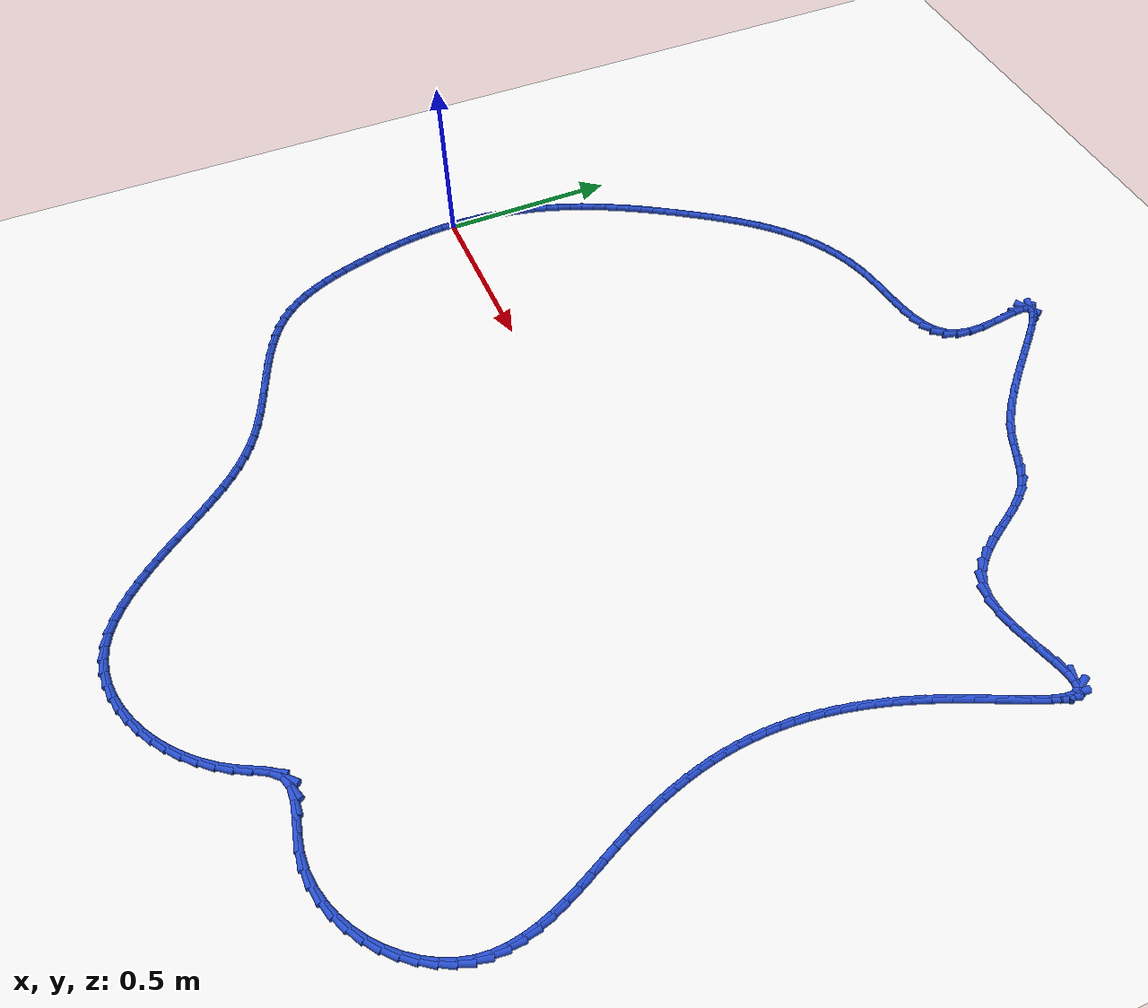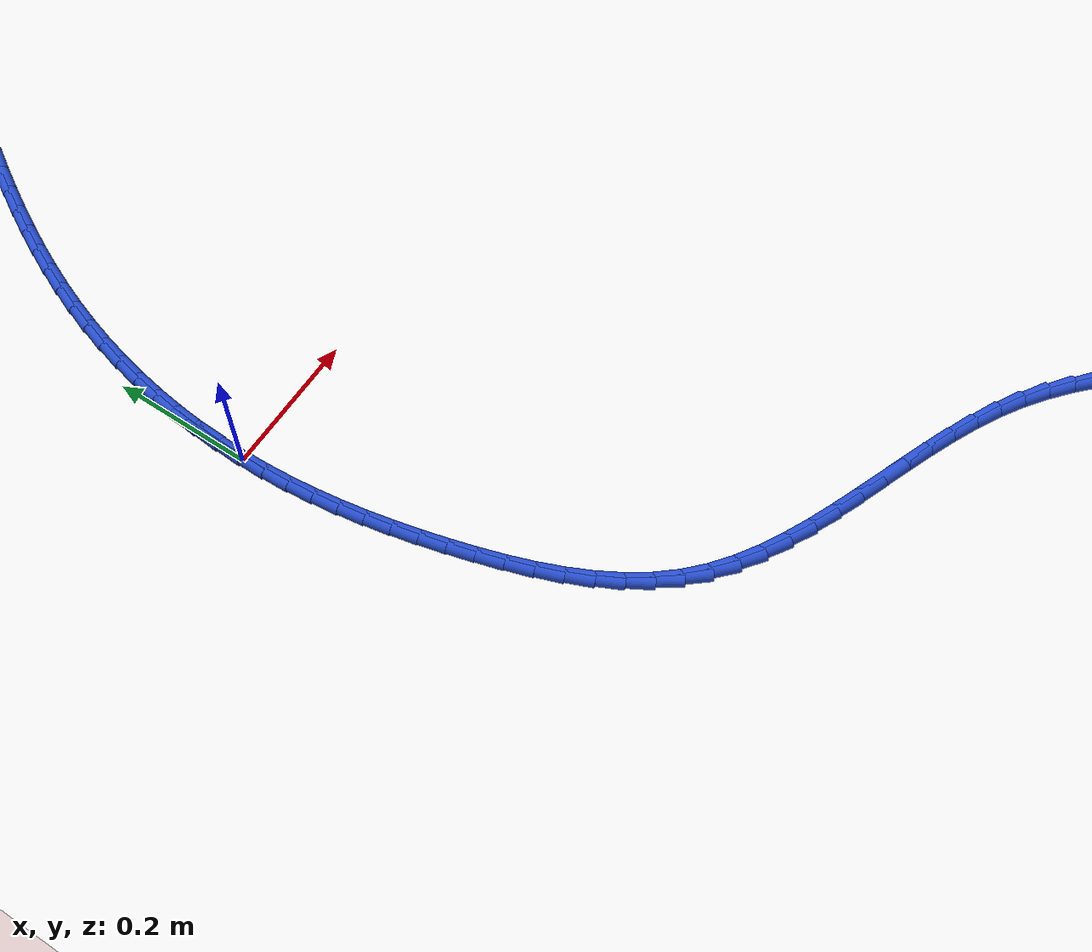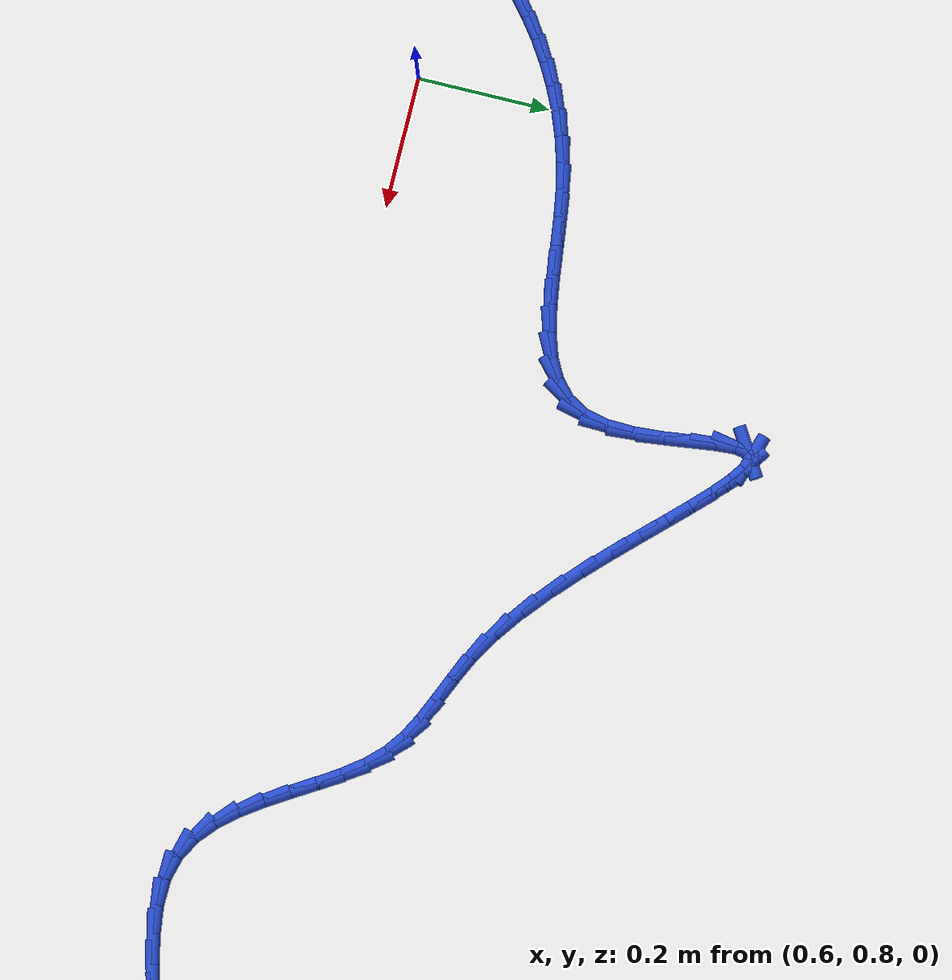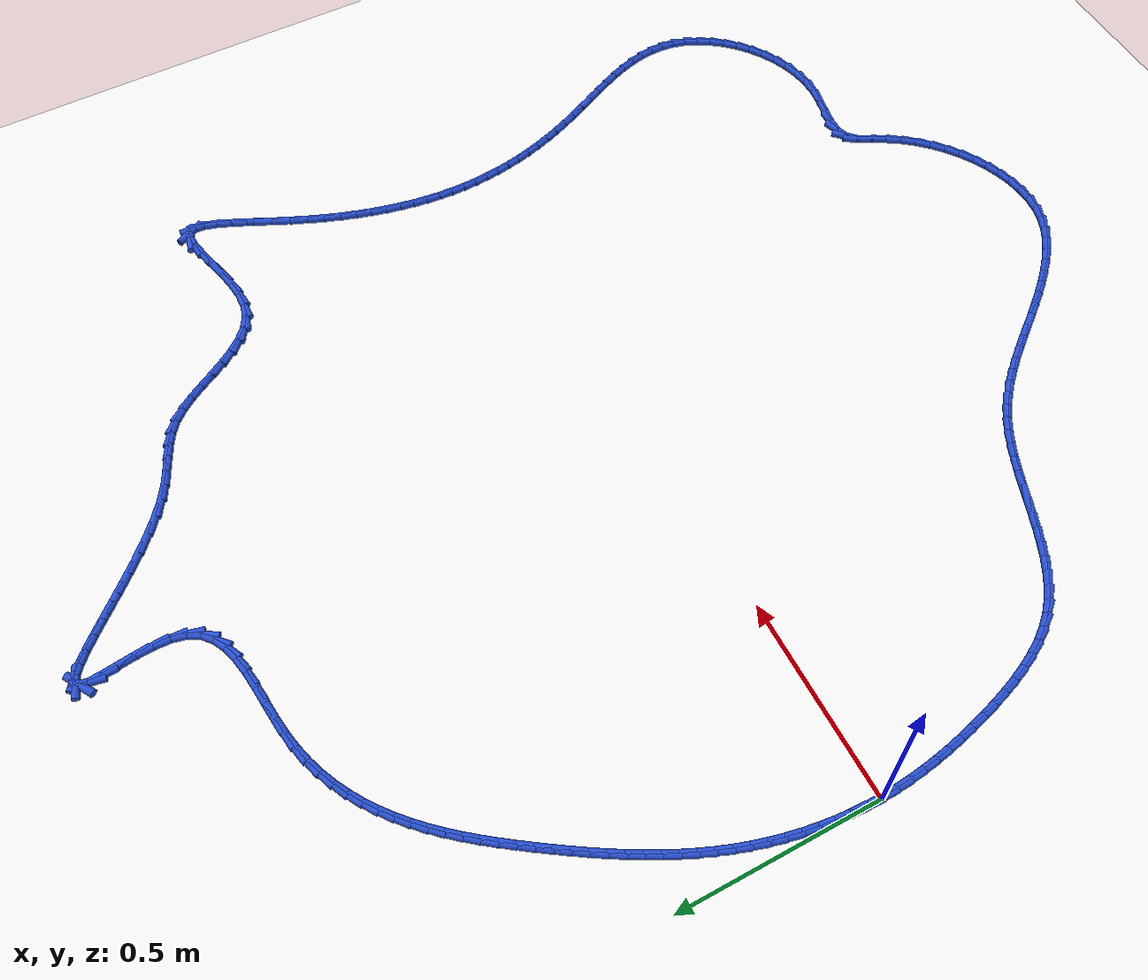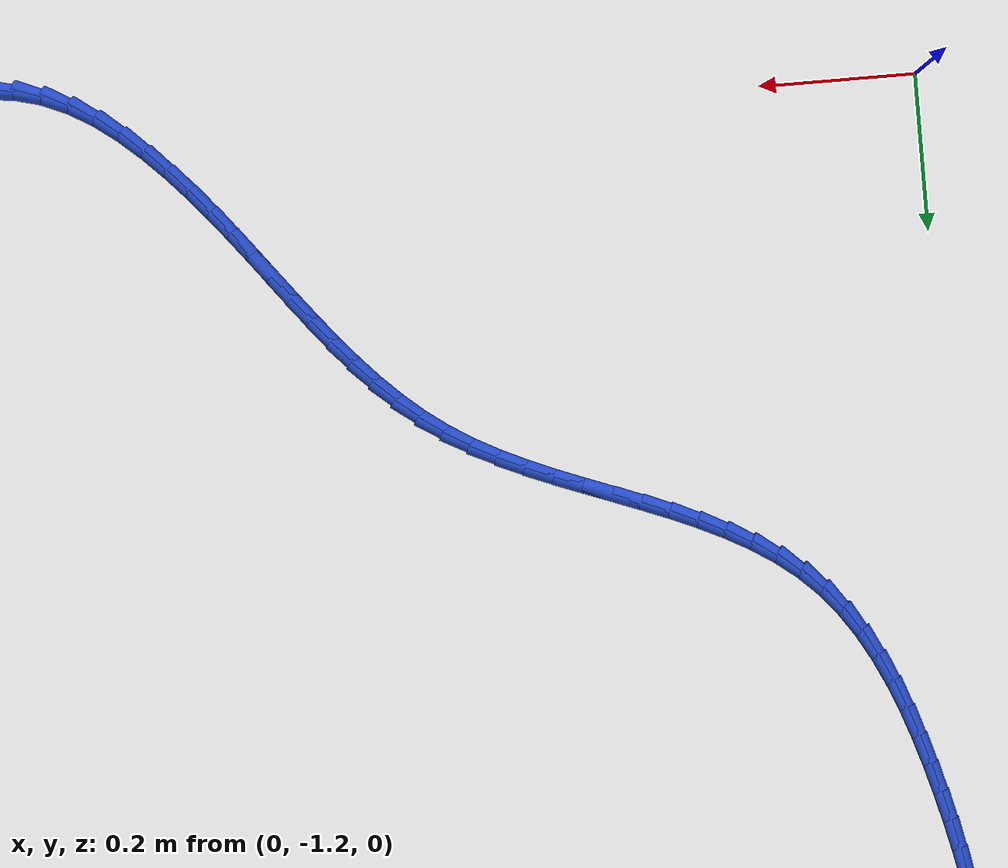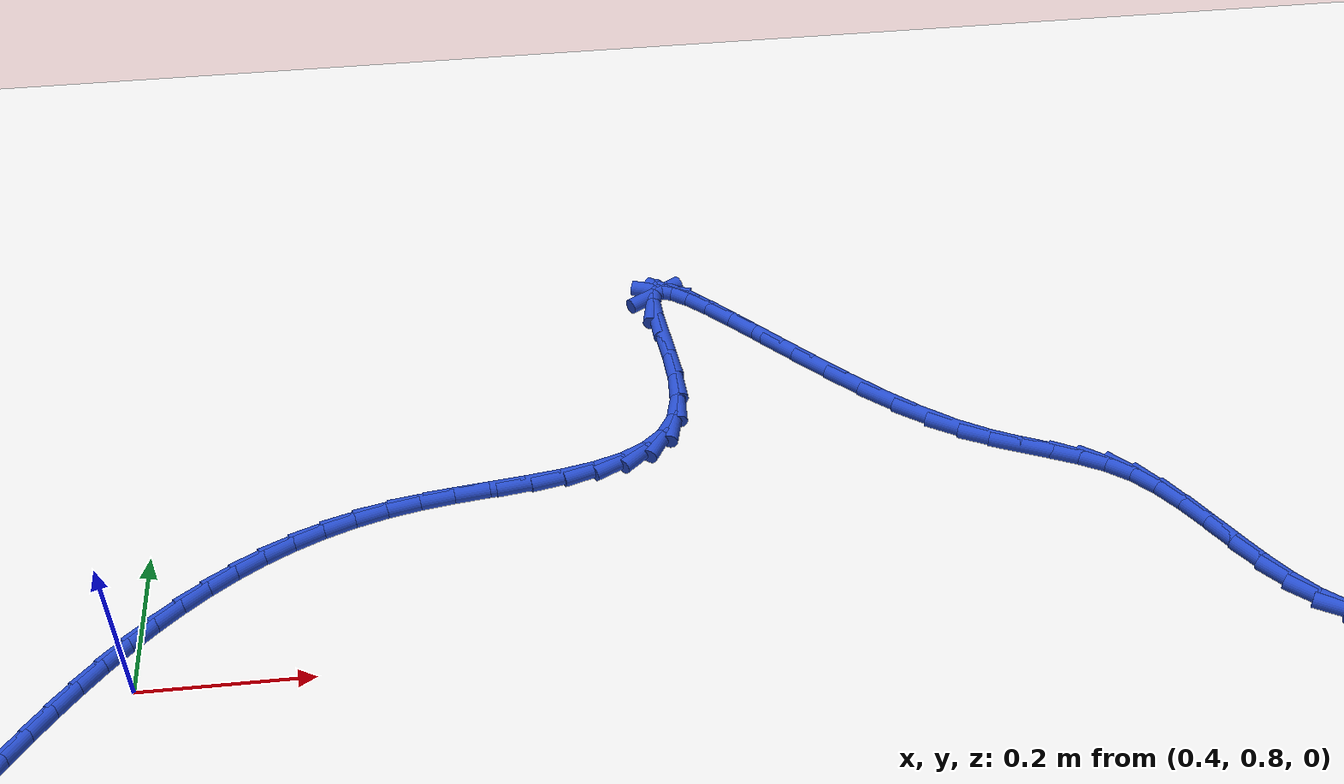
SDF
<sdf version="1.6">
 <world name="default">
  <light name="sun" type="directional">
   <pose>0 0 10 0 -0 0</pose>
   <diffuse>0.8 0.8 0.8 1</diffuse>
   <specular>0.2 0.2 0.2 1</specular>
   <attenuation>
    <range>1000</range>
    <constant>0.9</constant>
    <linear>0.01</linear>
    <quadratic>0.001</quadratic>
   </attenuation>
   <direction>-0.5 0.1 -0.9</direction>
  </light>
  <model name="ground_plane">
   <static>1</static>
   <link name="link">
    <collision name="collision">
     <geometry><plane><normal>0 0 1</normal><size>100 100</size></plane></geometry>
     <surface><friction><ode><mu>100</mu><mu2>50</mu2></ode></friction></surface>
    </collision>
    <visual name="visual">
     <cast_shadows>0</cast_shadows>
     <geometry><plane><normal>0 0 1</normal><size>100 100</size></plane></geometry>
     <material>
      <script><uri>file://media/materials/scripts/gazebo.material</uri><name>Gazebo/WhiteGlow</name></script>
     </material>
    </visual>
   </link>
  </model>
  <gravity>0 0 -9.8</gravity>
  <magnetic_field>6e-06 2.3e-05 -4.2e-05</magnetic_field>
  <atmosphere type="adiabatic"/>
  <physics name="default_physics" default="0" type="ode">
   <max_step_size>0.001</max_step_size>
   <real_time_factor>1</real_time_factor>
   <real_time_update_rate>1000</real_time_update_rate>
  </physics>
  <scene><ambient>0.4 0.4 0.4 1</ambient><background>0.7 0.7 0.7 1</background><shadows>1</shadows></scene>
  <spherical_coordinates>
   <surface_model>EARTH_WGS84</surface_model>
   <latitude_deg>0</latitude_deg>
   <longitude_deg>0</longitude_deg>
   <elevation>0</elevation>
   <heading_deg>0</heading_deg>
  </spherical_coordinates>
  <model name="line">
   <link name="link_0">
    <pose>-1.734723475976807e-18 6.245004513516506e-17 0.01 0 1.57 1.5594142094917165</pose>
    <collision name="collision">
     <geometry><cylinder><radius>0.01</radius><length>0.08</length></cylinder></geometry>
    </collision>
    <visual name="visual">
     <material>
      <script><name>Gazebo/Blue</name><uri>file://media/materials/scripts/gazebo.material</uri></script>
     </material>
     <geometry><cylinder><radius>0.01</radius><length>0.08</length></cylinder></geometry>
    </visual>
   </link>
   <link name="link_1">
    <pose>0.00041959633002896753 0.03686293145337743 0.01 0 1.57 1.5197614206529997</pose>
    <collision name="collision">
     <geometry><cylinder><radius>0.01</radius><length>0.08</length></cylinder></geometry>
    </collision>
    <visual name="visual">
     <material>
      <script><name>Gazebo/Blue</name><uri>file://media/materials/scripts/gazebo.material</uri></script>
     </material>
     <geometry><cylinder><radius>0.01</radius><length>0.08</length></cylinder></geometry>
    </visual>
   </link>
   <link name="link_2">
    <pose>0.0023075632535122246 0.07382444804384612 0.01 0 1.57 1.4806341923794002</pose>
    <collision name="collision">
     <geometry><cylinder><radius>0.01</radius><length>0.08</length></cylinder></geometry>
    </collision>
    <visual name="visual">
     <material>
      <script><name>Gazebo/Blue</name><uri>file://media/materials/scripts/gazebo.material</uri></script>
     </material>
     <geometry><cylinder><radius>0.01</radius><length>0.08</length></cylinder></geometry>
    </visual>
   </link>
   <link name="link_3">
    <pose>0.005649455353335342 0.11078931762957243 0.01 0 1.57 1.4418444868212625</pose>
    <collision name="collision">
     <geometry><cylinder><radius>0.01</radius><length>0.08</length></cylinder></geometry>
    </collision>
    <visual name="visual">
     <material>
      <script><name>Gazebo/Blue</name><uri>file://media/materials/scripts/gazebo.material</uri></script>
     </material>
     <geometry><cylinder><radius>0.01</radius><length>0.08</length></cylinder></geometry>
    </visual>
   </link>
   <link name="link_4">
    <pose>0.010430827212383897 0.14766230806872271 0.01 0 1.57 1.40320618219238</pose>
    <collision name="collision">
     <geometry><cylinder><radius>0.01</radius><length>0.08</length></cylinder></geometry>
    </collision>
    <visual name="visual">
     <material>
      <script><name>Gazebo/Blue</name><uri>file://media/materials/scripts/gazebo.material</uri></script>
     </material>
     <geometry><cylinder><radius>0.01</radius><length>0.08</length></cylinder></geometry>
    </visual>
   </link>
   <link name="link_5">
    <pose>0.016637233413543475 0.18434818721946336 0.01 0 1.57 1.3645342668743343</pose>
    <collision name="collision">
     <geometry><cylinder><radius>0.01</radius><length>0.08</length></cylinder></geometry>
    </collision>
    <visual name="visual">
     <material>
      <script><name>Gazebo/Blue</name><uri>file://media/materials/scripts/gazebo.material</uri></script>
     </material>
     <geometry><cylinder><radius>0.01</radius><length>0.08</length></cylinder></geometry>
    </visual>
   </link>
   <link name="link_6">
    <pose>0.02425422853969965 0.2207517229399607 0.01 0 1.57 1.3256439769377975</pose>
    <collision name="collision">
     <geometry><cylinder><radius>0.01</radius><length>0.08</length></cylinder></geometry>
    </collision>
    <visual name="visual">
     <material>
      <script><name>Gazebo/Blue</name><uri>file://media/materials/scripts/gazebo.material</uri></script>
     </material>
     <geometry><cylinder><radius>0.01</radius><length>0.08</length></cylinder></geometry>
    </visual>
   </link>
   <link name="link_7">
    <pose>0.033267367173738 0.25677768308838117 0.01 0 1.57 1.2863499621935641</pose>
    <collision name="collision">
     <geometry><cylinder><radius>0.01</radius><length>0.08</length></cylinder></geometry>
    </collision>
    <visual name="visual">
     <material>
      <script><name>Gazebo/Blue</name><uri>file://media/materials/scripts/gazebo.material</uri></script>
     </material>
     <geometry><cylinder><radius>0.01</radius><length>0.08</length></cylinder></geometry>
    </visual>
   </link>
   <link name="link_8">
    <pose>0.04366220389854408 0.29233083552289085 0.01 0 1.57 1.2468676575764424</pose>
    <collision name="collision">
     <geometry><cylinder><radius>0.01</radius><length>0.08</length></cylinder></geometry>
    </collision>
    <visual name="visual">
     <material>
      <script><name>Gazebo/Blue</name><uri>file://media/materials/scripts/gazebo.material</uri></script>
     </material>
     <geometry><cylinder><radius>0.01</radius><length>0.08</length></cylinder></geometry>
    </visual>
   </link>
   <link name="link_9">
    <pose>0.055414555991797405 0.327333573481135 0.01 0 1.57 1.2091093961100625</pose>
    <collision name="collision">
     <geometry><cylinder><radius>0.01</radius><length>0.08</length></cylinder></geometry>
    </collision>
    <visual name="visual">
     <material>
      <script><name>Gazebo/Blue</name><uri>file://media/materials/scripts/gazebo.material</uri></script>
     </material>
     <geometry><cylinder><radius>0.01</radius><length>0.08</length></cylinder></geometry>
    </visual>
   </link>
   <link name="link_10">
    <pose>0.06845234348073441 0.36179498843986807 0.01 0 1.57 1.1737942052509123</pose>
    <collision name="collision">
     <geometry><cylinder><radius>0.01</radius><length>0.08</length></cylinder></geometry>
    </collision>
    <visual name="visual">
     <material>
      <script><name>Gazebo/Blue</name><uri>file://media/materials/scripts/gazebo.material</uri></script>
     </material>
     <geometry><cylinder><radius>0.01</radius><length>0.08</length></cylinder></geometry>
    </visual>
   </link>
   <link name="link_11">
    <pose>0.0826887837965743 0.3957507848687246 0.01 0 1.57 1.1410190597035177</pose>
    <collision name="collision">
     <geometry><cylinder><radius>0.01</radius><length>0.08</length></cylinder></geometry>
    </collision>
    <visual name="visual">
     <material>
      <script><name>Gazebo/Blue</name><uri>file://media/materials/scripts/gazebo.material</uri></script>
     </material>
     <geometry><cylinder><radius>0.01</radius><length>0.08</length></cylinder></geometry>
    </visual>
   </link>
   <link name="link_12">
    <pose>0.0980370904534148 0.42923667432767404 0.01 0 1.57 1.110845754170046</pose>
    <collision name="collision">
     <geometry><cylinder><radius>0.01</radius><length>0.08</length></cylinder></geometry>
    </collision>
    <visual name="visual">
     <material>
      <script><name>Gazebo/Blue</name><uri>file://media/materials/scripts/gazebo.material</uri></script>
     </material>
     <geometry><cylinder><radius>0.01</radius><length>0.08</length></cylinder></geometry>
    </visual>
   </link>
   <link name="link_13">
    <pose>0.11441047696535372 0.4622883683766858 0.01 0 1.57 1.083306772269377</pose>
    <collision name="collision">
     <geometry><cylinder><radius>0.01</radius><length>0.08</length></cylinder></geometry>
    </collision>
    <visual name="visual">
     <material>
      <script><name>Gazebo/Blue</name><uri>file://media/materials/scripts/gazebo.material</uri></script>
     </material>
     <geometry><cylinder><radius>0.01</radius><length>0.08</length></cylinder></geometry>
    </visual>
   </link>
   <link name="link_14">
    <pose>0.13172215684648883 0.4949415785757296 0.01 0 1.57 1.0584112083198152</pose>
    <collision name="collision">
     <geometry><cylinder><radius>0.01</radius><length>0.08</length></cylinder></geometry>
    </collision>
    <visual name="visual">
     <material>
      <script><name>Gazebo/Blue</name><uri>file://media/materials/scripts/gazebo.material</uri></script>
     </material>
     <geometry><cylinder><radius>0.01</radius><length>0.08</length></cylinder></geometry>
    </visual>
   </link>
   <link name="link_15">
    <pose>0.14988534361091774 0.5272320164847746 0.01 0 1.57 1.0361505030005373</pose>
    <collision name="collision">
     <geometry><cylinder><radius>0.01</radius><length>0.08</length></cylinder></geometry>
    </collision>
    <visual name="visual">
     <material>
      <script><name>Gazebo/Blue</name><uri>file://media/materials/scripts/gazebo.material</uri></script>
     </material>
     <geometry><cylinder><radius>0.01</radius><length>0.08</length></cylinder></geometry>
    </visual>
   </link>
   <link name="link_16">
    <pose>0.1688132507727383 0.5591953936637903 0.01 0 1.57 1.0165037237975427</pose>
    <collision name="collision">
     <geometry><cylinder><radius>0.01</radius><length>0.08</length></cylinder></geometry>
    </collision>
    <visual name="visual">
     <material>
      <script><name>Gazebo/Blue</name><uri>file://media/materials/scripts/gazebo.material</uri></script>
     </material>
     <geometry><cylinder><radius>0.01</radius><length>0.08</length></cylinder></geometry>
    </visual>
   </link>
   <link name="link_17">
    <pose>0.18841909184604821 0.5908674216727464 0.01 0 1.57 0.9994422360289478</pose>
    <collision name="collision">
     <geometry><cylinder><radius>0.01</radius><length>0.08</length></cylinder></geometry>
    </collision>
    <visual name="visual">
     <material>
      <script><name>Gazebo/Blue</name><uri>file://media/materials/scripts/gazebo.material</uri></script>
     </material>
     <geometry><cylinder><radius>0.01</radius><length>0.08</length></cylinder></geometry>
    </visual>
   </link>
   <link name="link_18">
    <pose>0.2086160803449452 0.6222838120716119 0.01 0 1.57 0.9849337000167219</pose>
    <collision name="collision">
     <geometry><cylinder><radius>0.01</radius><length>0.08</length></cylinder></geometry>
    </collision>
    <visual name="visual">
     <material>
      <script><name>Gazebo/Blue</name><uri>file://media/materials/scripts/gazebo.material</uri></script>
     </material>
     <geometry><cylinder><radius>0.01</radius><length>0.08</length></cylinder></geometry>
    </visual>
   </link>
   <link name="link_19">
    <pose>0.229317429783527 0.6534802764203566 0.01 0 1.57 0.9729401917821159</pose>
    <collision name="collision">
     <geometry><cylinder><radius>0.01</radius><length>0.08</length></cylinder></geometry>
    </collision>
    <visual name="visual">
     <material>
      <script><name>Gazebo/Blue</name><uri>file://media/materials/scripts/gazebo.material</uri></script>
     </material>
     <geometry><cylinder><radius>0.01</radius><length>0.08</length></cylinder></geometry>
    </visual>
   </link>
   <link name="link_20">
    <pose>0.2504364964700212 0.6844923892473219 0.01 0 1.57 0.961520134958428</pose>
    <collision name="collision">
     <geometry><cylinder><radius>0.01</radius><length>0.08</length></cylinder></geometry>
    </collision>
    <visual name="visual">
     <material>
      <script><name>Gazebo/Blue</name><uri>file://media/materials/scripts/gazebo.material</uri></script>
     </material>
     <geometry><cylinder><radius>0.01</radius><length>0.08</length></cylinder></geometry>
    </visual>
   </link>
   <link name="link_21">
    <pose>0.2719390974156577 0.7153053814459571 0.01 0 1.57 0.9458832486209974</pose>
    <collision name="collision">
     <geometry><cylinder><radius>0.01</radius><length>0.08</length></cylinder></geometry>
    </collision>
    <visual name="visual">
     <material>
      <script><name>Gazebo/Blue</name><uri>file://media/materials/scripts/gazebo.material</uri></script>
     </material>
     <geometry><cylinder><radius>0.01</radius><length>0.08</length></cylinder></geometry>
    </visual>
   </link>
   <link name="link_22">
    <pose>0.2939215157018397 0.7457792828386856 0.01 0 1.57 0.9252342550421012</pose>
    <collision name="collision">
     <geometry><cylinder><radius>0.01</radius><length>0.08</length></cylinder></geometry>
    </collision>
    <visual name="visual">
     <material>
      <script><name>Gazebo/Blue</name><uri>file://media/materials/scripts/gazebo.material</uri></script>
     </material>
     <geometry><cylinder><radius>0.01</radius><length>0.08</length></cylinder></geometry>
    </visual>
   </link>
   <link name="link_23">
    <pose>0.31649997388245926 0.7757549884391035 0.01 0 1.57 0.8994755979723202</pose>
    <collision name="collision">
     <geometry><cylinder><radius>0.01</radius><length>0.08</length></cylinder></geometry>
    </collision>
    <visual name="visual">
     <material>
      <script><name>Gazebo/Blue</name><uri>file://media/materials/scripts/gazebo.material</uri></script>
     </material>
     <geometry><cylinder><radius>0.01</radius><length>0.08</length></cylinder></geometry>
    </visual>
   </link>
   <link name="link_24">
    <pose>0.3397906945114086 0.8050733932608068 0.01 0 1.57 0.8684958564985839</pose>
    <collision name="collision">
     <geometry><cylinder><radius>0.01</radius><length>0.08</length></cylinder></geometry>
    </collision>
    <visual name="visual">
     <material>
      <script><name>Gazebo/Blue</name><uri>file://media/materials/scripts/gazebo.material</uri></script>
     </material>
     <geometry><cylinder><radius>0.01</radius><length>0.08</length></cylinder></geometry>
    </visual>
   </link>
   <link name="link_25">
    <pose>0.36390990014257946 0.8335753923173913 0.01 0 1.57 0.8321895468190854</pose>
    <collision name="collision">
     <geometry><cylinder><radius>0.01</radius><length>0.08</length></cylinder></geometry>
    </collision>
    <visual name="visual">
     <material>
      <script><name>Gazebo/Blue</name><uri>file://media/materials/scripts/gazebo.material</uri></script>
     </material>
     <geometry><cylinder><radius>0.01</radius><length>0.08</length></cylinder></geometry>
    </visual>
   </link>
   <link name="link_26">
    <pose>0.3889738133298642 0.8611018806224535 0.01 0 1.57 0.7904827724453364</pose>
    <collision name="collision">
     <geometry><cylinder><radius>0.01</radius><length>0.08</length></cylinder></geometry>
    </collision>
    <visual name="visual">
     <material>
      <script><name>Gazebo/Blue</name><uri>file://media/materials/scripts/gazebo.material</uri></script>
     </material>
     <geometry><cylinder><radius>0.01</radius><length>0.08</length></cylinder></geometry>
    </visual>
   </link>
   <link name="link_27">
    <pose>0.41509865662715445 0.8874937531895888 0.01 0 1.57 0.7433649602911423</pose>
    <collision name="collision">
     <geometry><cylinder><radius>0.01</radius><length>0.08</length></cylinder></geometry>
    </collision>
    <visual name="visual">
     <material>
      <script><name>Gazebo/Blue</name><uri>file://media/materials/scripts/gazebo.material</uri></script>
     </material>
     <geometry><cylinder><radius>0.01</radius><length>0.08</length></cylinder></geometry>
    </visual>
   </link>
   <link name="link_28">
    <pose>0.44240065258834255 0.9125919050323932 0.01 0 1.57 0.6909256533400588</pose>
    <collision name="collision">
     <geometry><cylinder><radius>0.01</radius><length>0.08</length></cylinder></geometry>
    </collision>
    <visual name="visual">
     <material>
      <script><name>Gazebo/Blue</name><uri>file://media/materials/scripts/gazebo.material</uri></script>
     </material>
     <geometry><cylinder><radius>0.01</radius><length>0.08</length></cylinder></geometry>
    </visual>
   </link>
   <link name="link_29">
    <pose>0.47099602376732036 0.9362372311644629 0.01 0 1.57 0.6333933266414129</pose>
    <collision name="collision">
     <geometry><cylinder><radius>0.01</radius><length>0.08</length></cylinder></geometry>
    </collision>
    <visual name="visual">
     <material>
      <script><name>Gazebo/Blue</name><uri>file://media/materials/scripts/gazebo.material</uri></script>
     </material>
     <geometry><cylinder><radius>0.01</radius><length>0.08</length></cylinder></geometry>
    </visual>
   </link>
   <link name="link_30">
    <pose>0.50100099271798 0.9582706265993939 0.01 0 1.57 0.5711706503171893</pose>
    <collision name="collision">
     <geometry><cylinder><radius>0.01</radius><length>0.08</length></cylinder></geometry>
    </collision>
    <visual name="visual">
     <material>
      <script><name>Gazebo/Blue</name><uri>file://media/materials/scripts/gazebo.material</uri></script>
     </material>
     <geometry><cylinder><radius>0.01</radius><length>0.08</length></cylinder></geometry>
    </visual>
   </link>
   <link name="link_31">
    <pose>0.5325317819942132 0.9785329863507818 0.01 0 1.57 0.5048582418891413</pose>
    <collision name="collision">
     <geometry><cylinder><radius>0.01</radius><length>0.08</length></cylinder></geometry>
    </collision>
    <visual name="visual">
     <material>
      <script><name>Gazebo/Blue</name><uri>file://media/materials/scripts/gazebo.material</uri></script>
     </material>
     <geometry><cylinder><radius>0.01</radius><length>0.08</length></cylinder></geometry>
    </visual>
   </link>
   <link name="link_32">
    <pose>0.5657046141499125 0.996865205432223 0.01 0 1.57 0.43525797994208</pose>
    <collision name="collision">
     <geometry><cylinder><radius>0.01</radius><length>0.08</length></cylinder></geometry>
    </collision>
    <visual name="visual">
     <material>
      <script><name>Gazebo/Blue</name><uri>file://media/materials/scripts/gazebo.material</uri></script>
     </material>
     <geometry><cylinder><radius>0.01</radius><length>0.08</length></cylinder></geometry>
    </visual>
   </link>
   <link name="link_33">
    <pose>0.6006357117389699 1.0131081788573135 0.01 0 1.57 0.36334880359344923</pose>
    <collision name="collision">
     <geometry><cylinder><radius>0.01</radius><length>0.08</length></cylinder></geometry>
    </collision>
    <visual name="visual">
     <material>
      <script><name>Gazebo/Blue</name><uri>file://media/materials/scripts/gazebo.material</uri></script>
     </material>
     <geometry><cylinder><radius>0.01</radius><length>0.08</length></cylinder></geometry>
    </visual>
   </link>
   <link name="link_34">
    <pose>0.6374412973152767 1.0271028016396488 0.01 0 1.57 0.2902332632933607</pose>
    <collision name="collision">
     <geometry><cylinder><radius>0.01</radius><length>0.08</length></cylinder></geometry>
    </collision>
    <visual name="visual">
     <material>
      <script><name>Gazebo/Blue</name><uri>file://media/materials/scripts/gazebo.material</uri></script>
     </material>
     <geometry><cylinder><radius>0.01</radius><length>0.08</length></cylinder></geometry>
    </visual>
   </link>
   <link name="link_35">
    <pose>0.6762375934327256 1.0386899687928253 0.01 0 1.57 0.2170793369445838</pose>
    <collision name="collision">
     <geometry><cylinder><radius>0.01</radius><length>0.08</length></cylinder></geometry>
    </collision>
    <visual name="visual">
     <material>
      <script><name>Gazebo/Blue</name><uri>file://media/materials/scripts/gazebo.material</uri></script>
     </material>
     <geometry><cylinder><radius>0.01</radius><length>0.08</length></cylinder></geometry>
    </visual>
   </link>
   <link name="link_36">
    <pose>0.7171401828552437 1.0477112272027955 0.01 0 1.57 0.15352552423355653</pose>
    <collision name="collision">
     <geometry><cylinder><radius>0.01</radius><length>0.08</length></cylinder></geometry>
    </collision>
    <visual name="visual">
     <material>
      <script><name>Gazebo/Blue</name><uri>file://media/materials/scripts/gazebo.material</uri></script>
     </material>
     <geometry><cylinder><radius>0.01</radius><length>0.08</length></cylinder></geometry>
    </visual>
   </link>
   <link name="link_37">
    <pose>0.7599440002487562 1.0543348272722584 0.01 0 1.57 0.11966423342751442</pose>
    <collision name="collision">
     <geometry><cylinder><radius>0.01</radius><length>0.08</length></cylinder></geometry>
    </collision>
    <visual name="visual">
     <material>
      <script><name>Gazebo/Blue</name><uri>file://media/materials/scripts/gazebo.material</uri></script>
     </material>
     <geometry><cylinder><radius>0.01</radius><length>0.08</length></cylinder></geometry>
    </visual>
   </link>
   <link name="link_38">
    <pose>0.8036043631385684 1.0595844926603228 0.01 0 1.57 0.11572813520731863</pose>
    <collision name="collision">
     <geometry><cylinder><radius>0.01</radius><length>0.08</length></cylinder></geometry>
    </collision>
    <visual name="visual">
     <material>
      <script><name>Gazebo/Blue</name><uri>file://media/materials/scripts/gazebo.material</uri></script>
     </material>
     <geometry><cylinder><radius>0.01</radius><length>0.08</length></cylinder></geometry>
    </visual>
   </link>
   <link name="link_39">
    <pose>0.846940846189356 1.064622253381936 0.01 0 1.57 0.14217490254160253</pose>
    <collision name="collision">
     <geometry><cylinder><radius>0.01</radius><length>0.08</length></cylinder></geometry>
    </collision>
    <visual name="visual">
     <material>
      <script><name>Gazebo/Blue</name><uri>file://media/materials/scripts/gazebo.material</uri></script>
     </material>
     <geometry><cylinder><radius>0.01</radius><length>0.08</length></cylinder></geometry>
    </visual>
   </link>
   <link name="link_40">
    <pose>0.8887730240657946 1.0706101394520446 0.01 0 1.57 0.20403193153452104</pose>
    <collision name="collision">
     <geometry><cylinder><radius>0.01</radius><length>0.08</length></cylinder></geometry>
    </collision>
    <visual name="visual">
     <material>
      <script><name>Gazebo/Blue</name><uri>file://media/materials/scripts/gazebo.material</uri></script>
     </material>
     <geometry><cylinder><radius>0.01</radius><length>0.08</length></cylinder></geometry>
    </visual>
   </link>
   <link name="link_41">
    <pose>0.9279204714325598 1.0787101808855946 0.01 0 1.57 0.31185836564098296</pose>
    <collision name="collision">
     <geometry><cylinder><radius>0.01</radius><length>0.08</length></cylinder></geometry>
    </collision>
    <visual name="visual">
     <material>
      <script><name>Gazebo/Blue</name><uri>file://media/materials/scripts/gazebo.material</uri></script>
     </material>
     <geometry><cylinder><radius>0.01</radius><length>0.08</length></cylinder></geometry>
    </visual>
   </link>
   <link name="link_42">
    <pose>0.9632027629543278 1.0900844076975333 0.01 0 1.57 0.4817906622888758</pose>
    <collision name="collision">
     <geometry><cylinder><radius>0.01</radius><length>0.08</length></cylinder></geometry>
    </collision>
    <visual name="visual">
     <material>
      <script><name>Gazebo/Blue</name><uri>file://media/materials/scripts/gazebo.material</uri></script>
     </material>
     <geometry><cylinder><radius>0.01</radius><length>0.08</length></cylinder></geometry>
    </visual>
   </link>
   <link name="link_43">
    <pose>0.9934394732957734 1.1058948499028072 0.01 0 1.57 0.7281720508403067</pose>
    <collision name="collision">
     <geometry><cylinder><radius>0.01</radius><length>0.08</length></cylinder></geometry>
    </collision>
    <visual name="visual">
     <material>
      <script><name>Gazebo/Blue</name><uri>file://media/materials/scripts/gazebo.material</uri></script>
     </material>
     <geometry><cylinder><radius>0.01</radius><length>0.08</length></cylinder></geometry>
    </visual>
   </link>
   <link name="link_44">
    <pose>1.017450177121573 1.127303537516363 0.01 0 1.57 1.0381682753477155</pose>
    <collision name="collision">
     <geometry><cylinder><radius>0.01</radius><length>0.08</length></cylinder></geometry>
    </collision>
    <visual name="visual">
     <material>
      <script><name>Gazebo/Blue</name><uri>file://media/materials/scripts/gazebo.material</uri></script>
     </material>
     <geometry><cylinder><radius>0.01</radius><length>0.08</length></cylinder></geometry>
    </visual>
   </link>
   <link name="link_45">
    <pose>1.0340544490964019 1.155472500553147 0.01 0 1.57 1.3415848188188524</pose>
    <collision name="collision">
     <geometry><cylinder><radius>0.01</radius><length>0.08</length></cylinder></geometry>
    </collision>
    <visual name="visual">
     <material>
      <script><name>Gazebo/Blue</name><uri>file://media/materials/scripts/gazebo.material</uri></script>
     </material>
     <geometry><cylinder><radius>0.01</radius><length>0.08</length></cylinder></geometry>
    </visual>
   </link>
   <link name="link_46">
    <pose>1.0423836287068127 1.1911722797754847 0.01 0 1.57 1.5352115632065804</pose>
    <collision name="collision">
     <geometry><cylinder><radius>0.01</radius><length>0.08</length></cylinder></geometry>
    </collision>
    <visual name="visual">
     <material>
      <script><name>Gazebo/Blue</name><uri>file://media/materials/scripts/gazebo.material</uri></script>
     </material>
     <geometry><cylinder><radius>0.01</radius><length>0.08</length></cylinder></geometry>
    </visual>
   </link>
   <link name="link_47">
    <pose>1.0438481756337614 1.232311479643305 0.01 0 1.57 -1.502000540450538</pose>
    <collision name="collision">
     <geometry><cylinder><radius>0.01</radius><length>0.08</length></cylinder></geometry>
    </collision>
    <visual name="visual">
     <material>
      <script><name>Gazebo/Blue</name><uri>file://media/materials/scripts/gazebo.material</uri></script>
     </material>
     <geometry><cylinder><radius>0.01</radius><length>0.08</length></cylinder></geometry>
    </visual>
   </link>
   <link name="link_48">
    <pose>1.0408703503264782 1.275528166381375 0.01 0 1.57 -1.45225654680116</pose>
    <collision name="collision">
     <geometry><cylinder><radius>0.01</radius><length>0.08</length></cylinder></geometry>
    </collision>
    <visual name="visual">
     <material>
      <script><name>Gazebo/Blue</name><uri>file://media/materials/scripts/gazebo.material</uri></script>
     </material>
     <geometry><cylinder><radius>0.01</radius><length>0.08</length></cylinder></geometry>
    </visual>
   </link>
   <link name="link_49">
    <pose>1.035876981495017 1.3174546697589975 0.01 0 1.57 -1.4484628603315188</pose>
    <collision name="collision">
     <geometry><cylinder><radius>0.01</radius><length>0.08</length></cylinder></geometry>
    </collision>
    <visual name="visual">
     <material>
      <script><name>Gazebo/Blue</name><uri>file://media/materials/scripts/gazebo.material</uri></script>
     </material>
     <geometry><cylinder><radius>0.01</radius><length>0.08</length></cylinder></geometry>
    </visual>
   </link>
   <link name="link_50">
    <pose>1.0312948978494307 1.3547233195454786 0.01 0 1.57 -1.5112299644052511</pose>
    <collision name="collision">
     <geometry><cylinder><radius>0.01</radius><length>0.08</length></cylinder></geometry>
    </collision>
    <visual name="visual">
     <material>
      <script><name>Gazebo/Blue</name><uri>file://media/materials/scripts/gazebo.material</uri></script>
     </material>
     <geometry><cylinder><radius>0.01</radius><length>0.08</length></cylinder></geometry>
    </visual>
   </link>
   <link name="link_51">
    <pose>1.0295509280997723 1.3839664455101222 0.01 0 1.57 1.380746014200417</pose>
    <collision name="collision">
     <geometry><cylinder><radius>0.01</radius><length>0.08</length></cylinder></geometry>
    </collision>
    <visual name="visual">
     <material>
      <script><name>Gazebo/Blue</name><uri>file://media/materials/scripts/gazebo.material</uri></script>
     </material>
     <geometry><cylinder><radius>0.01</radius><length>0.08</length></cylinder></geometry>
    </visual>
   </link>
   <link name="link_52">
    <pose>1.0330054869559417 1.4019241454276252 0.01 0 1.57 0.5448765193451922</pose>
    <collision name="collision">
     <geometry><cylinder><radius>0.01</radius><length>0.08</length></cylinder></geometry>
    </collision>
    <visual name="visual">
     <material>
      <script><name>Gazebo/Blue</name><uri>file://media/materials/scripts/gazebo.material</uri></script>
     </material>
     <geometry><cylinder><radius>0.01</radius><length>0.08</length></cylinder></geometry>
    </visual>
   </link>
   <link name="link_53">
    <pose>1.0425550873327927 1.407711946593216 0.01 0 1.57 -0.31637296207430277</pose>
    <collision name="collision">
     <geometry><cylinder><radius>0.01</radius><length>0.08</length></cylinder></geometry>
    </collision>
    <visual name="visual">
     <material>
      <script><name>Gazebo/Blue</name><uri>file://media/materials/scripts/gazebo.material</uri></script>
     </material>
     <geometry><cylinder><radius>0.01</radius><length>0.08</length></cylinder></geometry>
    </visual>
   </link>
   <link name="link_54">
    <pose>1.0576668361381854 1.4027648305423797 0.01 0 1.57 -0.613841902767912</pose>
    <collision name="collision">
     <geometry><cylinder><radius>0.01</radius><length>0.08</length></cylinder></geometry>
    </collision>
    <visual name="visual">
     <material>
      <script><name>Gazebo/Blue</name><uri>file://media/materials/scripts/gazebo.material</uri></script>
     </material>
     <geometry><cylinder><radius>0.01</radius><length>0.08</length></cylinder></geometry>
    </visual>
   </link>
   <link name="link_55">
    <pose>1.0777483266673082 1.3886143497642618 0.01 0 1.57 -0.728491891102244</pose>
    <collision name="collision">
     <geometry><cylinder><radius>0.01</radius><length>0.08</length></cylinder></geometry>
    </collision>
    <visual name="visual">
     <material>
      <script><name>Gazebo/Blue</name><uri>file://media/materials/scripts/gazebo.material</uri></script>
     </material>
     <geometry><cylinder><radius>0.01</radius><length>0.08</length></cylinder></geometry>
    </visual>
   </link>
   <link name="link_56">
    <pose>1.1022071522153511 1.366792056748008 0.01 0 1.57 -0.7803951883285504</pose>
    <collision name="collision">
     <geometry><cylinder><radius>0.01</radius><length>0.08</length></cylinder></geometry>
    </collision>
    <visual name="visual">
     <material>
      <script><name>Gazebo/Blue</name><uri>file://media/materials/scripts/gazebo.material</uri></script>
     </material>
     <geometry><cylinder><radius>0.01</radius><length>0.08</length></cylinder></geometry>
    </visual>
   </link>
   <link name="link_57">
    <pose>1.1304509060775019 1.338829503982765 0.01 0 1.57 -0.8031283511208743</pose>
    <collision name="collision">
     <geometry><cylinder><radius>0.01</radius><length>0.08</length></cylinder></geometry>
    </collision>
    <visual name="visual">
     <material>
      <script><name>Gazebo/Blue</name><uri>file://media/materials/scripts/gazebo.material</uri></script>
     </material>
     <geometry><cylinder><radius>0.01</radius><length>0.08</length></cylinder></geometry>
    </visual>
   </link>
   <link name="link_58">
    <pose>1.1618871815489493 1.306258243957677 0.01 0 1.57 -0.8085271217908689</pose>
    <collision name="collision">
     <geometry><cylinder><radius>0.01</radius><length>0.08</length></cylinder></geometry>
    </collision>
    <visual name="visual">
     <material>
      <script><name>Gazebo/Blue</name><uri>file://media/materials/scripts/gazebo.material</uri></script>
     </material>
     <geometry><cylinder><radius>0.01</radius><length>0.08</length></cylinder></geometry>
    </visual>
   </link>
   <link name="link_59">
    <pose>1.1959235719248824 1.2706098291618904 0.01 0 1.57 -0.801097966855747</pose>
    <collision name="collision">
     <geometry><cylinder><radius>0.01</radius><length>0.08</length></cylinder></geometry>
    </collision>
    <visual name="visual">
     <material>
      <script><name>Gazebo/Blue</name><uri>file://media/materials/scripts/gazebo.material</uri></script>
     </material>
     <geometry><cylinder><radius>0.01</radius><length>0.08</length></cylinder></geometry>
    </visual>
   </link>
   <link name="link_60">
    <pose>1.2319676705004912 1.23341581208455 0.01 0 1.57 -0.782032142534381</pose>
    <collision name="collision">
     <geometry><cylinder><radius>0.01</radius><length>0.08</length></cylinder></geometry>
    </collision>
    <visual name="visual">
     <material>
      <script><name>Gazebo/Blue</name><uri>file://media/materials/scripts/gazebo.material</uri></script>
     </material>
     <geometry><cylinder><radius>0.01</radius><length>0.08</length></cylinder></geometry>
    </visual>
   </link>
   <link name="link_61">
    <pose>1.2694270705709623 1.1962077452148026 0.01 0 1.57 -0.750376251048214</pose>
    <collision name="collision">
     <geometry><cylinder><radius>0.01</radius><length>0.08</length></cylinder></geometry>
    </collision>
    <visual name="visual">
     <material>
      <script><name>Gazebo/Blue</name><uri>file://media/materials/scripts/gazebo.material</uri></script>
     </material>
     <geometry><cylinder><radius>0.01</radius><length>0.08</length></cylinder></geometry>
    </visual>
   </link>
   <link name="link_62">
    <pose>1.3077093654314864 1.1605171810417936 0.01 0 1.57 -0.7030699892687395</pose>
    <collision name="collision">
     <geometry><cylinder><radius>0.01</radius><length>0.08</length></cylinder></geometry>
    </collision>
    <visual name="visual">
     <material>
      <script><name>Gazebo/Blue</name><uri>file://media/materials/scripts/gazebo.material</uri></script>
     </material>
     <geometry><cylinder><radius>0.01</radius><length>0.08</length></cylinder></geometry>
    </visual>
   </link>
   <link name="link_63">
    <pose>1.346222148377252 1.1278756720546679 0.01 0 1.57 -0.6341723387397363</pose>
    <collision name="collision">
     <geometry><cylinder><radius>0.01</radius><length>0.08</length></cylinder></geometry>
    </collision>
    <visual name="visual">
     <material>
      <script><name>Gazebo/Blue</name><uri>file://media/materials/scripts/gazebo.material</uri></script>
     </material>
     <geometry><cylinder><radius>0.01</radius><length>0.08</length></cylinder></geometry>
    </visual>
   </link>
   <link name="link_64">
    <pose>1.3843730127034477 1.0998147707425723 0.01 0 1.57 -0.5386966603337799</pose>
    <collision name="collision">
     <geometry><cylinder><radius>0.01</radius><length>0.08</length></cylinder></geometry>
    </collision>
    <visual name="visual">
     <material>
      <script><name>Gazebo/Blue</name><uri>file://media/materials/scripts/gazebo.material</uri></script>
     </material>
     <geometry><cylinder><radius>0.01</radius><length>0.08</length></cylinder></geometry>
    </visual>
   </link>
   <link name="link_65">
    <pose>1.421590855276233 1.0775711789595939 0.01 0 1.57 -0.45377471875242775</pose>
    <collision name="collision">
     <geometry><cylinder><radius>0.01</radius><length>0.08</length></cylinder></geometry>
    </collision>
    <visual name="visual">
     <material>
      <script><name>Gazebo/Blue</name><uri>file://media/materials/scripts/gazebo.material</uri></script>
     </material>
     <geometry><cylinder><radius>0.01</radius><length>0.08</length></cylinder></geometry>
    </visual>
   </link>
   <link name="link_66">
    <pose>1.4574714815310066 1.060071511781243 0.01 0 1.57 -0.4111279789276704</pose>
    <collision name="collision">
     <geometry><cylinder><radius>0.01</radius><length>0.08</length></cylinder></geometry>
    </collision>
    <visual name="visual">
     <material>
      <script><name>Gazebo/Blue</name><uri>file://media/materials/scripts/gazebo.material</uri></script>
     </material>
     <geometry><cylinder><radius>0.01</radius><length>0.08</length></cylinder></geometry>
    </visual>
   </link>
   <link name="link_67">
    <pose>1.4916893756426919 1.045153436503021 0.01 0 1.57 -0.42289680968629967</pose>
    <collision name="collision">
     <geometry><cylinder><radius>0.01</radius><length>0.08</length></cylinder></geometry>
    </collision>
    <visual name="visual">
     <material>
      <script><name>Gazebo/Blue</name><uri>file://media/materials/scripts/gazebo.material</uri></script>
     </material>
     <geometry><cylinder><radius>0.01</radius><length>0.08</length></cylinder></geometry>
    </visual>
   </link>
   <link name="link_68">
    <pose>1.523919483813063 1.0306482257690492 0.01 0 1.57 -0.4978659021485133</pose>
    <collision name="collision">
     <geometry><cylinder><radius>0.01</radius><length>0.08</length></cylinder></geometry>
    </collision>
    <visual name="visual">
     <material>
      <script><name>Gazebo/Blue</name><uri>file://media/materials/scripts/gazebo.material</uri></script>
     </material>
     <geometry><cylinder><radius>0.01</radius><length>0.08</length></cylinder></geometry>
    </visual>
   </link>
   <link name="link_69">
    <pose>1.5538367522438925 1.014387152223447 0.01 0 1.57 -0.6370447020658595</pose>
    <collision name="collision">
     <geometry><cylinder><radius>0.01</radius><length>0.08</length></cylinder></geometry>
    </collision>
    <visual name="visual">
     <material>
      <script><name>Gazebo/Blue</name><uri>file://media/materials/scripts/gazebo.material</uri></script>
     </material>
     <geometry><cylinder><radius>0.01</radius><length>0.08</length></cylinder></geometry>
    </visual>
   </link>
   <link name="link_70">
    <pose>1.581116129215657 0.9942014951621901 0.01 0 1.57 -0.8071825467529306</pose>
    <collision name="collision">
     <geometry><cylinder><radius>0.01</radius><length>0.08</length></cylinder></geometry>
    </collision>
    <visual name="visual">
     <material>
      <script><name>Gazebo/Blue</name><uri>file://media/materials/scripts/gazebo.material</uri></script>
     </material>
     <geometry><cylinder><radius>0.01</radius><length>0.08</length></cylinder></geometry>
    </visual>
   </link>
   <link name="link_71">
    <pose>1.6056397282249038 0.9685854623789829 0.01 0 1.57 -0.9300030060966878</pose>
    <collision name="collision">
     <geometry><cylinder><radius>0.01</radius><length>0.08</length></cylinder></geometry>
    </collision>
    <visual name="visual">
     <material>
      <script><name>Gazebo/Blue</name><uri>file://media/materials/scripts/gazebo.material</uri></script>
     </material>
     <geometry><cylinder><radius>0.01</radius><length>0.08</length></cylinder></geometry>
    </visual>
   </link>
   <link name="link_72">
    <pose>1.6280653245290417 0.9385153785771043 0.01 0 1.57 -1.000021395005159</pose>
    <collision name="collision">
     <geometry><cylinder><radius>0.01</radius><length>0.08</length></cylinder></geometry>
    </collision>
    <visual name="visual">
     <material>
      <script><name>Gazebo/Blue</name><uri>file://media/materials/scripts/gazebo.material</uri></script>
     </material>
     <geometry><cylinder><radius>0.01</radius><length>0.08</length></cylinder></geometry>
    </visual>
   </link>
   <link name="link_73">
    <pose>1.6492321963015202 0.9055483776214603 0.01 0 1.57 -1.026883010544404</pose>
    <collision name="collision">
     <geometry><cylinder><radius>0.01</radius><length>0.08</length></cylinder></geometry>
    </collision>
    <visual name="visual">
     <material>
      <script><name>Gazebo/Blue</name><uri>file://media/materials/scripts/gazebo.material</uri></script>
     </material>
     <geometry><cylinder><radius>0.01</radius><length>0.08</length></cylinder></geometry>
    </visual>
   </link>
   <link name="link_74">
    <pose>1.6699796217157856 0.8712415933769566 0.01 0 1.57 -1.0151268811893586</pose>
    <collision name="collision">
     <geometry><cylinder><radius>0.01</radius><length>0.08</length></cylinder></geometry>
    </collision>
    <visual name="visual">
     <material>
      <script><name>Gazebo/Blue</name><uri>file://media/materials/scripts/gazebo.material</uri></script>
     </material>
     <geometry><cylinder><radius>0.01</radius><length>0.08</length></cylinder></geometry>
    </visual>
   </link>
   <link name="link_75">
    <pose>1.691146878945286 0.8371521597084984 0.01 0 1.57 -0.9641129038287042</pose>
    <collision name="collision">
     <geometry><cylinder><radius>0.01</radius><length>0.08</length></cylinder></geometry>
    </collision>
    <visual name="visual">
     <material>
      <script><name>Gazebo/Blue</name><uri>file://media/materials/scripts/gazebo.material</uri></script>
     </material>
     <geometry><cylinder><radius>0.01</radius><length>0.08</length></cylinder></geometry>
    </visual>
   </link>
   <link name="link_76">
    <pose>1.7135732461634703 0.8048372104809913 0.01 0 1.57 -0.8685313839008822</pose>
    <collision name="collision">
     <geometry><cylinder><radius>0.01</radius><length>0.08</length></cylinder></geometry>
    </collision>
    <visual name="visual">
     <material>
      <script><name>Gazebo/Blue</name><uri>file://media/materials/scripts/gazebo.material</uri></script>
     </material>
     <geometry><cylinder><radius>0.01</radius><length>0.08</length></cylinder></geometry>
    </visual>
   </link>
   <link name="link_77">
    <pose>1.7380980015437844 0.775853879559341 0.01 0 1.57 -0.7201681286227198</pose>
    <collision name="collision">
     <geometry><cylinder><radius>0.01</radius><length>0.08</length></cylinder></geometry>
    </collision>
    <visual name="visual">
     <material>
      <script><name>Gazebo/Blue</name><uri>file://media/materials/scripts/gazebo.material</uri></script>
     </material>
     <geometry><cylinder><radius>0.01</radius><length>0.08</length></cylinder></geometry>
    </visual>
   </link>
   <link name="link_78">
    <pose>1.7655604232596773 0.751759300808453 0.01 0 1.57 -0.5142489492076203</pose>
    <collision name="collision">
     <geometry><cylinder><radius>0.01</radius><length>0.08</length></cylinder></geometry>
    </collision>
    <visual name="visual">
     <material>
      <script><name>Gazebo/Blue</name><uri>file://media/materials/scripts/gazebo.material</uri></script>
     </material>
     <geometry><cylinder><radius>0.01</radius><length>0.08</length></cylinder></geometry>
    </visual>
   </link>
   <link name="link_79">
    <pose>1.7967997894845977 0.7341106080932328 0.01 0 1.57 -0.26281188434732417</pose>
    <collision name="collision">
     <geometry><cylinder><radius>0.01</radius><length>0.08</length></cylinder></geometry>
    </collision>
    <visual name="visual">
     <material>
      <script><name>Gazebo/Blue</name><uri>file://media/materials/scripts/gazebo.material</uri></script>
     </material>
     <geometry><cylinder><radius>0.01</radius><length>0.08</length></cylinder></geometry>
    </visual>
   </link>
   <link name="link_80">
    <pose>1.8326549398146046 0.724464329275963 0.01 0 1.57 -0.023806323502087272</pose>
    <collision name="collision">
     <geometry><cylinder><radius>0.01</radius><length>0.08</length></cylinder></geometry>
    </collision>
    <visual name="visual">
     <material>
      <script><name>Gazebo/Blue</name><uri>file://media/materials/scripts/gazebo.material</uri></script>
     </material>
     <geometry><cylinder><radius>0.01</radius><length>0.08</length></cylinder></geometry>
    </visual>
   </link>
   <link name="link_81">
    <pose>1.873327043071354 0.7234958930705628 0.01 0 1.57 0.13040840547339128</pose>
    <collision name="collision">
     <geometry><cylinder><radius>0.01</radius><length>0.08</length></cylinder></geometry>
    </collision>
    <visual name="visual">
     <material>
      <script><name>Gazebo/Blue</name><uri>file://media/materials/scripts/gazebo.material</uri></script>
     </material>
     <geometry><cylinder><radius>0.01</radius><length>0.08</length></cylinder></geometry>
    </visual>
   </link>
   <link name="link_82">
    <pose>1.9171042262596691 0.7292373899931744 0.01 0 1.57 0.2193369366691486</pose>
    <collision name="collision">
     <geometry><cylinder><radius>0.01</radius><length>0.08</length></cylinder></geometry>
    </collision>
    <visual name="visual">
     <material>
      <script><name>Gazebo/Blue</name><uri>file://media/materials/scripts/gazebo.material</uri></script>
     </material>
     <geometry><cylinder><radius>0.01</radius><length>0.08</length></cylinder></geometry>
    </visual>
   </link>
   <link name="link_83">
    <pose>1.961917367703103 0.7392272835639213 0.01 0 1.57 0.26277826136028576</pose>
    <collision name="collision">
     <geometry><cylinder><radius>0.01</radius><length>0.08</length></cylinder></geometry>
    </collision>
    <visual name="visual">
     <material>
      <script><name>Gazebo/Blue</name><uri>file://media/materials/scripts/gazebo.material</uri></script>
     </material>
     <geometry><cylinder><radius>0.01</radius><length>0.08</length></cylinder></geometry>
    </visual>
   </link>
   <link name="link_84">
    <pose>2.005697345725211 0.7510040373029271 0.01 0 1.57 0.2664387800928989</pose>
    <collision name="collision">
     <geometry><cylinder><radius>0.01</radius><length>0.08</length></cylinder></geometry>
    </collision>
    <visual name="visual">
     <material>
      <script><name>Gazebo/Blue</name><uri>file://media/materials/scripts/gazebo.material</uri></script>
     </material>
     <geometry><cylinder><radius>0.01</radius><length>0.08</length></cylinder></geometry>
    </visual>
   </link>
   <link name="link_85">
    <pose>2.0463750386495496 0.7621061147303156 0.01 0 1.57 0.2206964636185534</pose>
    <collision name="collision">
     <geometry><cylinder><radius>0.01</radius><length>0.08</length></cylinder></geometry>
    </collision>
    <visual name="visual">
     <material>
      <script><name>Gazebo/Blue</name><uri>file://media/materials/scripts/gazebo.material</uri></script>
     </material>
     <geometry><cylinder><radius>0.01</radius><length>0.08</length></cylinder></geometry>
    </visual>
   </link>
   <link name="link_86">
    <pose>2.0818813247996704 0.77007197936621 0.01 0 1.57 0.08358515946901968</pose>
    <collision name="collision">
     <geometry><cylinder><radius>0.01</radius><length>0.08</length></cylinder></geometry>
    </collision>
    <visual name="visual">
     <material>
      <script><name>Gazebo/Blue</name><uri>file://media/materials/scripts/gazebo.material</uri></script>
     </material>
     <geometry><cylinder><radius>0.01</radius><length>0.08</length></cylinder></geometry>
    </visual>
   </link>
   <link name="link_87">
    <pose>2.1101470824991297 0.772440094730734 0.01 0 1.57 -0.29166673585404285</pose>
    <collision name="collision">
     <geometry><cylinder><radius>0.01</radius><length>0.08</length></cylinder></geometry>
    </collision>
    <visual name="visual">
     <material>
      <script><name>Gazebo/Blue</name><uri>file://media/materials/scripts/gazebo.material</uri></script>
     </material>
     <geometry><cylinder><radius>0.01</radius><length>0.08</length></cylinder></geometry>
    </visual>
   </link>
   <link name="link_88">
    <pose>2.129103190071482 0.7667489243440111 0.01 0 1.57 -1.1016557000606213</pose>
    <collision name="collision">
     <geometry><cylinder><radius>0.01</radius><length>0.08</length></cylinder></geometry>
    </collision>
    <visual name="visual">
     <material>
      <script><name>Gazebo/Blue</name><uri>file://media/materials/scripts/gazebo.material</uri></script>
     </material>
     <geometry><cylinder><radius>0.01</radius><length>0.08</length></cylinder></geometry>
    </visual>
   </link>
   <link name="link_89">
    <pose>2.13710007454467 0.7509724060009757 0.01 0 1.57 1.4932194195515063</pose>
    <collision name="collision">
     <geometry><cylinder><radius>0.01</radius><length>0.08</length></cylinder></geometry>
    </collision>
    <visual name="visual">
     <material>
      <script><name>Gazebo/Blue</name><uri>file://media/materials/scripts/gazebo.material</uri></script>
     </material>
     <geometry><cylinder><radius>0.01</radius><length>0.08</length></cylinder></geometry>
    </visual>
   </link>
   <link name="link_90">
    <pose>2.1351467707306804 0.7258440028738392 0.01 0 1.57 1.2777819757225566</pose>
    <collision name="collision">
     <geometry><cylinder><radius>0.01</radius><length>0.08</length></cylinder></geometry>
    </collision>
    <visual name="visual">
     <material>
      <script><name>Gazebo/Blue</name><uri>file://media/materials/scripts/gazebo.material</uri></script>
     </material>
     <geometry><cylinder><radius>0.01</radius><length>0.08</length></cylinder></geometry>
    </visual>
   </link>
   <link name="link_91">
    <pose>2.1252905175461856 0.693174791233995 0.01 0 1.57 1.1824344360607957</pose>
    <collision name="collision">
     <geometry><cylinder><radius>0.01</radius><length>0.08</length></cylinder></geometry>
    </collision>
    <visual name="visual">
     <material>
      <script><name>Gazebo/Blue</name><uri>file://media/materials/scripts/gazebo.material</uri></script>
     </material>
     <geometry><cylinder><radius>0.01</radius><length>0.08</length></cylinder></geometry>
    </visual>
   </link>
   <link name="link_92">
    <pose>2.109580934330799 0.6547783181338066 0.01 0 1.57 1.138670818970482</pose>
    <collision name="collision">
     <geometry><cylinder><radius>0.01</radius><length>0.08</length></cylinder></geometry>
    </collision>
    <visual name="visual">
     <material>
      <script><name>Gazebo/Blue</name><uri>file://media/materials/scripts/gazebo.material</uri></script>
     </material>
     <geometry><cylinder><radius>0.01</radius><length>0.08</length></cylinder></geometry>
    </visual>
   </link>
   <link name="link_93">
    <pose>2.090067640424137 0.6124681306256387 0.01 0 1.57 1.1241841920452187</pose>
    <collision name="collision">
     <geometry><cylinder><radius>0.01</radius><length>0.08</length></cylinder></geometry>
    </collision>
    <visual name="visual">
     <material>
      <script><name>Gazebo/Blue</name><uri>file://media/materials/scripts/gazebo.material</uri></script>
     </material>
     <geometry><cylinder><radius>0.01</radius><length>0.08</length></cylinder></geometry>
    </visual>
   </link>
   <link name="link_94">
    <pose>2.0688002551658156 0.5680577757618556 0.01 0 1.57 1.1320503994265492</pose>
    <collision name="collision">
     <geometry><cylinder><radius>0.01</radius><length>0.08</length></cylinder></geometry>
    </collision>
    <visual name="visual">
     <material>
      <script><name>Gazebo/Blue</name><uri>file://media/materials/scripts/gazebo.material</uri></script>
     </material>
     <geometry><cylinder><radius>0.01</radius><length>0.08</length></cylinder></geometry>
    </visual>
   </link>
   <link name="link_95">
    <pose>2.047824630730444 0.5233574013210074 0.01 0 1.57 1.156094486937873</pose>
    <collision name="collision">
     <geometry><cylinder><radius>0.01</radius><length>0.08</length></cylinder></geometry>
    </collision>
    <visual name="visual">
     <material>
      <script><name>Gazebo/Blue</name><uri>file://media/materials/scripts/gazebo.material</uri></script>
     </material>
     <geometry><cylinder><radius>0.01</radius><length>0.08</length></cylinder></geometry>
    </visual>
   </link>
   <link name="link_96">
    <pose>2.028570541992315 0.4796212422318486 0.01 0 1.57 1.183788707067085</pose>
    <collision name="collision">
     <geometry><cylinder><radius>0.01</radius><length>0.08</length></cylinder></geometry>
    </collision>
    <visual name="visual">
     <material>
      <script><name>Gazebo/Blue</name><uri>file://media/materials/scripts/gazebo.material</uri></script>
     </material>
     <geometry><cylinder><radius>0.01</radius><length>0.08</length></cylinder></geometry>
    </visual>
   </link>
   <link name="link_97">
    <pose>2.01117358858686 0.43693574385387096 0.01 0 1.57 1.2134644137332158</pose>
    <collision name="collision">
     <geometry><cylinder><radius>0.01</radius><length>0.08</length></cylinder></geometry>
    </collision>
    <visual name="visual">
     <material>
      <script><name>Gazebo/Blue</name><uri>file://media/materials/scripts/gazebo.material</uri></script>
     </material>
     <geometry><cylinder><radius>0.01</radius><length>0.08</length></cylinder></geometry>
    </visual>
   </link>
   <link name="link_98">
    <pose>1.9956060752997251 0.39524000363217643 0.01 0 1.57 1.2451475450937168</pose>
    <collision name="collision">
     <geometry><cylinder><radius>0.01</radius><length>0.08</length></cylinder></geometry>
    </collision>
    <visual name="visual">
     <material>
      <script><name>Gazebo/Blue</name><uri>file://media/materials/scripts/gazebo.material</uri></script>
     </material>
     <geometry><cylinder><radius>0.01</radius><length>0.08</length></cylinder></geometry>
    </visual>
   </link>
   <link name="link_99">
    <pose>1.9818403069165513 0.3544731190118684 0.01 0 1.57 1.2788328422086663</pose>
    <collision name="collision">
     <geometry><cylinder><radius>0.01</radius><length>0.08</length></cylinder></geometry>
    </collision>
    <visual name="visual">
     <material>
      <script><name>Gazebo/Blue</name><uri>file://media/materials/scripts/gazebo.material</uri></script>
     </material>
     <geometry><cylinder><radius>0.01</radius><length>0.08</length></cylinder></geometry>
    </visual>
   </link>
   <link name="link_100">
    <pose>1.9698485882229835 0.31457418743804916 0.01 0 1.57 1.3144770356960842</pose>
    <collision name="collision">
     <geometry><cylinder><radius>0.01</radius><length>0.08</length></cylinder></geometry>
    </collision>
    <visual name="visual">
     <material>
      <script><name>Gazebo/Blue</name><uri>file://media/materials/scripts/gazebo.material</uri></script>
     </material>
     <geometry><cylinder><radius>0.01</radius><length>0.08</length></cylinder></geometry>
    </visual>
   </link>
   <link name="link_101">
    <pose>1.9596032240046624 0.2754823063558203 0.01 0 1.57 1.351992419440996</pose>
    <collision name="collision">
     <geometry><cylinder><radius>0.01</radius><length>0.08</length></cylinder></geometry>
    </collision>
    <visual name="visual">
     <material>
      <script><name>Gazebo/Blue</name><uri>file://media/materials/scripts/gazebo.material</uri></script>
     </material>
     <geometry><cylinder><radius>0.01</radius><length>0.08</length></cylinder></geometry>
    </visual>
   </link>
   <link name="link_102">
    <pose>1.9510765190472328 0.23713657321028517 0.01 0 1.57 1.3912415287960167</pose>
    <collision name="collision">
     <geometry><cylinder><radius>0.01</radius><length>0.08</length></cylinder></geometry>
    </collision>
    <visual name="visual">
     <material>
      <script><name>Gazebo/Blue</name><uri>file://media/materials/scripts/gazebo.material</uri></script>
     </material>
     <geometry><cylinder><radius>0.01</radius><length>0.08</length></cylinder></geometry>
    </visual>
   </link>
   <link name="link_103">
    <pose>1.944240778136336 0.1994760854465459 0.01 0 1.57 1.4320337570011614</pose>
    <collision name="collision">
     <geometry><cylinder><radius>0.01</radius><length>0.08</length></cylinder></geometry>
    </collision>
    <visual name="visual">
     <material>
      <script><name>Gazebo/Blue</name><uri>file://media/materials/scripts/gazebo.material</uri></script>
     </material>
     <geometry><cylinder><radius>0.01</radius><length>0.08</length></cylinder></geometry>
    </visual>
   </link>
   <link name="link_104">
    <pose>1.9390683060576166 0.16243994050970476 0.01 0 1.57 1.4741247549731071</pose>
    <collision name="collision">
     <geometry><cylinder><radius>0.01</radius><length>0.08</length></cylinder></geometry>
    </collision>
    <visual name="visual">
     <material>
      <script><name>Gazebo/Blue</name><uri>file://media/materials/scripts/gazebo.material</uri></script>
     </material>
     <geometry><cylinder><radius>0.01</radius><length>0.08</length></cylinder></geometry>
    </visual>
   </link>
   <link name="link_105">
    <pose>1.935531407596716 0.12596723584486424 0.01 0 1.57 1.517219317856337</pose>
    <collision name="collision">
     <geometry><cylinder><radius>0.01</radius><length>0.08</length></cylinder></geometry>
    </collision>
    <visual name="visual">
     <material>
      <script><name>Gazebo/Blue</name><uri>file://media/materials/scripts/gazebo.material</uri></script>
     </material>
     <geometry><cylinder><radius>0.01</radius><length>0.08</length></cylinder></geometry>
    </visual>
   </link>
   <link name="link_106">
    <pose>1.933602387539278 0.08999706889712598 0.01 0 1.57 1.560978142878517</pose>
    <collision name="collision">
     <geometry><cylinder><radius>0.01</radius><length>0.08</length></cylinder></geometry>
    </collision>
    <visual name="visual">
     <material>
      <script><name>Gazebo/Blue</name><uri>file://media/materials/scripts/gazebo.material</uri></script>
     </material>
     <geometry><cylinder><radius>0.01</radius><length>0.08</length></cylinder></geometry>
    </visual>
   </link>
   <link name="link_107">
    <pose>1.933253550670945 0.05446853711159397 0.01 0 1.57 -1.5365642855692117</pose>
    <collision name="collision">
     <geometry><cylinder><radius>0.01</radius><length>0.08</length></cylinder></geometry>
    </collision>
    <visual name="visual">
     <material>
      <script><name>Gazebo/Blue</name><uri>file://media/materials/scripts/gazebo.material</uri></script>
     </material>
     <geometry><cylinder><radius>0.01</radius><length>0.08</length></cylinder></geometry>
    </visual>
   </link>
   <link name="link_108">
    <pose>1.9344572017773605 0.019320737933369872 0.01 0 1.57 -1.4926154082358138</pose>
    <collision name="collision">
     <geometry><cylinder><radius>0.01</radius><length>0.08</length></cylinder></geometry>
    </collision>
    <visual name="visual">
     <material>
      <script><name>Gazebo/Blue</name><uri>file://media/materials/scripts/gazebo.material</uri></script>
     </material>
     <geometry><cylinder><radius>0.01</radius><length>0.08</length></cylinder></geometry>
    </visual>
   </link>
   <link name="link_109">
    <pose>1.9371856456441678 -0.015507231192443932 0.01 0 1.57 -1.4491648674850988</pose>
    <collision name="collision">
     <geometry><cylinder><radius>0.01</radius><length>0.08</length></cylinder></geometry>
    </collision>
    <visual name="visual">
     <material>
      <script><name>Gazebo/Blue</name><uri>file://media/materials/scripts/gazebo.material</uri></script>
     </material>
     <geometry><cylinder><radius>0.01</radius><length>0.08</length></cylinder></geometry>
    </visual>
   </link>
   <link name="link_110">
    <pose>1.941411187057008 -0.050076272820745005 0.01 0 1.57 -1.4065977870085</pose>
    <collision name="collision">
     <geometry><cylinder><radius>0.01</radius><length>0.08</length></cylinder></geometry>
    </collision>
    <visual name="visual">
     <material>
      <script><name>Gazebo/Blue</name><uri>file://media/materials/scripts/gazebo.material</uri></script>
     </material>
     <geometry><cylinder><radius>0.01</radius><length>0.08</length></cylinder></geometry>
    </visual>
   </link>
   <link name="link_111">
    <pose>1.9471061308015265 -0.08444728950643095 0.01 0 1.57 -1.3652724532759568</pose>
    <collision name="collision">
     <geometry><cylinder><radius>0.01</radius><length>0.08</length></cylinder></geometry>
    </collision>
    <visual name="visual">
     <material>
      <script><name>Gazebo/Blue</name><uri>file://media/materials/scripts/gazebo.material</uri></script>
     </material>
     <geometry><cylinder><radius>0.01</radius><length>0.08</length></cylinder></geometry>
    </visual>
   </link>
   <link name="link_112">
    <pose>1.9542427816633638 -0.11868118380440007 0.01 0 1.57 -1.3255078677519274</pose>
    <collision name="collision">
     <geometry><cylinder><radius>0.01</radius><length>0.08</length></cylinder></geometry>
    </collision>
    <visual name="visual">
     <material>
      <script><name>Gazebo/Blue</name><uri>file://media/materials/scripts/gazebo.material</uri></script>
     </material>
     <geometry><cylinder><radius>0.01</radius><length>0.08</length></cylinder></geometry>
    </visual>
   </link>
   <link name="link_113">
    <pose>1.9627934444281647 -0.1528388582695484 0.01 0 1.57 -1.2875747793883623</pose>
    <collision name="collision">
     <geometry><cylinder><radius>0.01</radius><length>0.08</length></cylinder></geometry>
    </collision>
    <visual name="visual">
     <material>
      <script><name>Gazebo/Blue</name><uri>file://media/materials/scripts/gazebo.material</uri></script>
     </material>
     <geometry><cylinder><radius>0.01</radius><length>0.08</length></cylinder></geometry>
    </visual>
   </link>
   <link name="link_114">
    <pose>1.972730423881572 -0.18698121545677435 0.01 0 1.57 -1.25169060369161</pose>
    <collision name="collision">
     <geometry><cylinder><radius>0.01</radius><length>0.08</length></cylinder></geometry>
    </collision>
    <visual name="visual">
     <material>
      <script><name>Gazebo/Blue</name><uri>file://media/materials/scripts/gazebo.material</uri></script>
     </material>
     <geometry><cylinder><radius>0.01</radius><length>0.08</length></cylinder></geometry>
    </visual>
   </link>
   <link name="link_115">
    <pose>1.984026024809227 -0.2211691579209754 0.01 0 1.57 -1.218018100830749</pose>
    <collision name="collision">
     <geometry><cylinder><radius>0.01</radius><length>0.08</length></cylinder></geometry>
    </collision>
    <visual name="visual">
     <material>
      <script><name>Gazebo/Blue</name><uri>file://media/materials/scripts/gazebo.material</uri></script>
     </material>
     <geometry><cylinder><radius>0.01</radius><length>0.08</length></cylinder></geometry>
    </visual>
   </link>
   <link name="link_116">
    <pose>1.9966525519967742 -0.25546358821704923 0.01 0 1.57 -1.1866672708235273</pose>
    <collision name="collision">
     <geometry><cylinder><radius>0.01</radius><length>0.08</length></cylinder></geometry>
    </collision>
    <visual name="visual">
     <material>
      <script><name>Gazebo/Blue</name><uri>file://media/materials/scripts/gazebo.material</uri></script>
     </material>
     <geometry><cylinder><radius>0.01</radius><length>0.08</length></cylinder></geometry>
    </visual>
   </link>
   <link name="link_117">
    <pose>2.010582310229856 -0.2899254088998934 0.01 0 1.57 -1.1576996809943494</pose>
    <collision name="collision">
     <geometry><cylinder><radius>0.01</radius><length>0.08</length></cylinder></geometry>
    </collision>
    <visual name="visual">
     <material>
      <script><name>Gazebo/Blue</name><uri>file://media/materials/scripts/gazebo.material</uri></script>
     </material>
     <geometry><cylinder><radius>0.01</radius><length>0.08</length></cylinder></geometry>
    </visual>
   </link>
   <link name="link_118">
    <pose>2.025787604294115 -0.3246155225244054 0.01 0 1.57 -1.132495735612264</pose>
    <collision name="collision">
     <geometry><cylinder><radius>0.01</radius><length>0.08</length></cylinder></geometry>
    </collision>
    <visual name="visual">
     <material>
      <script><name>Gazebo/Blue</name><uri>file://media/materials/scripts/gazebo.material</uri></script>
     </material>
     <geometry><cylinder><radius>0.01</radius><length>0.08</length></cylinder></geometry>
    </visual>
   </link>
   <link name="link_119">
    <pose>2.0421768383542247 -0.3595824944784238 0.01 0 1.57 -1.118825105426862</pose>
    <collision name="collision">
     <geometry><cylinder><radius>0.01</radius><length>0.08</length></cylinder></geometry>
    </collision>
    <visual name="visual">
     <material>
      <script><name>Gazebo/Blue</name><uri>file://media/materials/scripts/gazebo.material</uri></script>
     </material>
     <geometry><cylinder><radius>0.01</radius><length>0.08</length></cylinder></geometry>
    </visual>
   </link>
   <link name="link_120">
    <pose>2.059274950083748 -0.39480085502945583 0.01 0 1.57 -1.1189372080922677</pose>
    <collision name="collision">
     <geometry><cylinder><radius>0.01</radius><length>0.08</length></cylinder></geometry>
    </collision>
    <visual name="visual">
     <material>
      <script><name>Gazebo/Blue</name><uri>file://media/materials/scripts/gazebo.material</uri></script>
     </material>
     <geometry><cylinder><radius>0.01</radius><length>0.08</length></cylinder></geometry>
    </visual>
   </link>
   <link name="link_121">
    <pose>2.0764644907861776 -0.43021764418892366 0.01 0 1.57 -1.1326096687831506</pose>
    <collision name="collision">
     <geometry><cylinder><radius>0.01</radius><length>0.08</length></cylinder></geometry>
    </collision>
    <visual name="visual">
     <material>
      <script><name>Gazebo/Blue</name><uri>file://media/materials/scripts/gazebo.material</uri></script>
     </material>
     <geometry><cylinder><radius>0.01</radius><length>0.08</length></cylinder></geometry>
    </visual>
   </link>
   <link name="link_122">
    <pose>2.093127776078562 -0.465779856464731 0.01 0 1.57 -1.160260221847756</pose>
    <collision name="collision">
     <geometry><cylinder><radius>0.01</radius><length>0.08</length></cylinder></geometry>
    </collision>
    <visual name="visual">
     <material>
      <script><name>Gazebo/Blue</name><uri>file://media/materials/scripts/gazebo.material</uri></script>
     </material>
     <geometry><cylinder><radius>0.01</radius><length>0.08</length></cylinder></geometry>
    </visual>
   </link>
   <link name="link_123">
    <pose>2.1086471215779485 -0.5014344863647816 0.01 0 1.57 -1.2029089812999347</pose>
    <collision name="collision">
     <geometry><cylinder><radius>0.01</radius><length>0.08</length></cylinder></geometry>
    </collision>
    <visual name="visual">
     <material>
      <script><name>Gazebo/Blue</name><uri>file://media/materials/scripts/gazebo.material</uri></script>
     </material>
     <geometry><cylinder><radius>0.01</radius><length>0.08</length></cylinder></geometry>
    </visual>
   </link>
   <link name="link_124">
    <pose>2.1224048429013864 -0.5371285283969793 0.01 0 1.57 -1.2620936176630924</pose>
    <collision name="collision">
     <geometry><cylinder><radius>0.01</radius><length>0.08</length></cylinder></geometry>
    </collision>
    <visual name="visual">
     <material>
      <script><name>Gazebo/Blue</name><uri>file://media/materials/scripts/gazebo.material</uri></script>
     </material>
     <geometry><cylinder><radius>0.01</radius><length>0.08</length></cylinder></geometry>
    </visual>
   </link>
   <link name="link_125">
    <pose>2.1337832556659233 -0.5728089770692286 0.01 0 1.57 -1.339660683928909</pose>
    <collision name="collision">
     <geometry><cylinder><radius>0.01</radius><length>0.08</length></cylinder></geometry>
    </collision>
    <visual name="visual">
     <material>
      <script><name>Gazebo/Blue</name><uri>file://media/materials/scripts/gazebo.material</uri></script>
     </material>
     <geometry><cylinder><radius>0.01</radius><length>0.08</length></cylinder></geometry>
    </visual>
   </link>
   <link name="link_126">
    <pose>2.1421646754886083 -0.6084228268894316 0.01 0 1.57 -1.4372988602923291</pose>
    <collision name="collision">
     <geometry><cylinder><radius>0.01</radius><length>0.08</length></cylinder></geometry>
    </collision>
    <visual name="visual">
     <material>
      <script><name>Gazebo/Blue</name><uri>file://media/materials/scripts/gazebo.material</uri></script>
     </material>
     <geometry><cylinder><radius>0.01</radius><length>0.08</length></cylinder></geometry>
    </visual>
   </link>
   <link name="link_127">
    <pose>2.146931417986489 -0.643917072365493 0.01 0 1.57 -1.5556684875766635</pose>
    <collision name="collision">
     <geometry><cylinder><radius>0.01</radius><length>0.08</length></cylinder></geometry>
    </collision>
    <visual name="visual">
     <material>
      <script><name>Gazebo/Blue</name><uri>file://media/materials/scripts/gazebo.material</uri></script>
     </material>
     <geometry><cylinder><radius>0.01</radius><length>0.08</length></cylinder></geometry>
    </visual>
   </link>
   <link name="link_128">
    <pose>2.1474657987766137 -0.6792387080053166 0.01 0 1.57 1.4484431895576104</pose>
    <collision name="collision">
     <geometry><cylinder><radius>0.01</radius><length>0.08</length></cylinder></geometry>
    </collision>
    <visual name="visual">
     <material>
      <script><name>Gazebo/Blue</name><uri>file://media/materials/scripts/gazebo.material</uri></script>
     </material>
     <geometry><cylinder><radius>0.01</radius><length>0.08</length></cylinder></geometry>
    </visual>
   </link>
   <link name="link_129">
    <pose>2.1431501334760306 -0.714334728316806 0.01 0 1.57 1.2999803305079474</pose>
    <collision name="collision">
     <geometry><cylinder><radius>0.01</radius><length>0.08</length></cylinder></geometry>
    </collision>
    <visual name="visual">
     <material>
      <script><name>Gazebo/Blue</name><uri>file://media/materials/scripts/gazebo.material</uri></script>
     </material>
     <geometry><cylinder><radius>0.01</radius><length>0.08</length></cylinder></geometry>
    </visual>
   </link>
   <link name="link_130">
    <pose>2.133498762770912 -0.7490973015410576 0.01 0 1.57 1.1611290758077635</pose>
    <collision name="collision">
     <geometry><cylinder><radius>0.01</radius><length>0.08</length></cylinder></geometry>
    </collision>
    <visual name="visual">
     <material>
      <script><name>Gazebo/Blue</name><uri>file://media/materials/scripts/gazebo.material</uri></script>
     </material>
     <geometry><cylinder><radius>0.01</radius><length>0.08</length></cylinder></geometry>
    </visual>
   </link>
   <link name="link_131">
    <pose>2.11872045647949 -0.7831302191955147 0.01 0 1.57 1.0352894594895294</pose>
    <collision name="collision">
     <geometry><cylinder><radius>0.01</radius><length>0.08</length></cylinder></geometry>
    </collision>
    <visual name="visual">
     <material>
      <script><name>Gazebo/Blue</name><uri>file://media/materials/scripts/gazebo.material</uri></script>
     </material>
     <geometry><cylinder><radius>0.01</radius><length>0.08</length></cylinder></geometry>
    </visual>
   </link>
   <link name="link_132">
    <pose>2.099251495986804 -0.8159427936964466 0.01 0 1.57 0.9191740378306853</pose>
    <collision name="collision">
     <geometry><cylinder><radius>0.01</radius><length>0.08</length></cylinder></geometry>
    </collision>
    <visual name="visual">
     <material>
      <script><name>Gazebo/Blue</name><uri>file://media/materials/scripts/gazebo.material</uri></script>
     </material>
     <geometry><cylinder><radius>0.01</radius><length>0.08</length></cylinder></geometry>
    </visual>
   </link>
   <link name="link_133">
    <pose>2.0755282943523317 -0.847044282779457 0.01 0 1.57 0.8094653625543714</pose>
    <collision name="collision">
     <geometry><cylinder><radius>0.01</radius><length>0.08</length></cylinder></geometry>
    </collision>
    <visual name="visual">
     <material>
      <script><name>Gazebo/Blue</name><uri>file://media/materials/scripts/gazebo.material</uri></script>
     </material>
     <geometry><cylinder><radius>0.01</radius><length>0.08</length></cylinder></geometry>
    </visual>
   </link>
   <link name="link_134">
    <pose>2.047987264635555 -0.8759439441801534 0.01 0 1.57 0.7030469076351508</pose>
    <collision name="collision">
     <geometry><cylinder><radius>0.01</radius><length>0.08</length></cylinder></geometry>
    </collision>
    <visual name="visual">
     <material>
      <script><name>Gazebo/Blue</name><uri>file://media/materials/scripts/gazebo.material</uri></script>
     </material>
     <geometry><cylinder><radius>0.01</radius><length>0.08</length></cylinder></geometry>
    </visual>
   </link>
   <link name="link_135">
    <pose>2.017064819895954 -0.9021510356341418 0.01 0 1.57 0.5970537972132473</pose>
    <collision name="collision">
     <geometry><cylinder><radius>0.01</radius><length>0.08</length></cylinder></geometry>
    </collision>
    <visual name="visual">
     <material>
      <script><name>Gazebo/Blue</name><uri>file://media/materials/scripts/gazebo.material</uri></script>
     </material>
     <geometry><cylinder><radius>0.01</radius><length>0.08</length></cylinder></geometry>
    </visual>
   </link>
   <link name="link_136">
    <pose>1.9831973731930082 -0.9251748148770279 0.01 0 1.57 0.48886884635844946</pose>
    <collision name="collision">
     <geometry><cylinder><radius>0.01</radius><length>0.08</length></cylinder></geometry>
    </collision>
    <visual name="visual">
     <material>
      <script><name>Gazebo/Blue</name><uri>file://media/materials/scripts/gazebo.material</uri></script>
     </material>
     <geometry><cylinder><radius>0.01</radius><length>0.08</length></cylinder></geometry>
    </visual>
   </link>
   <link name="link_137">
    <pose>1.9468213375861982 -0.9445245396444181 0.01 0 1.57 0.37614101794132515</pose>
    <collision name="collision">
     <geometry><cylinder><radius>0.01</radius><length>0.08</length></cylinder></geometry>
    </collision>
    <visual name="visual">
     <material>
      <script><name>Gazebo/Blue</name><uri>file://media/materials/scripts/gazebo.material</uri></script>
     </material>
     <geometry><cylinder><radius>0.01</radius><length>0.08</length></cylinder></geometry>
    </visual>
   </link>
   <link name="link_138">
    <pose>1.9083731261350034 -0.9597094676719191 0.01 0 1.57 0.2568797689287992</pose>
    <collision name="collision">
     <geometry><cylinder><radius>0.01</radius><length>0.08</length></cylinder></geometry>
    </collision>
    <visual name="visual">
     <material>
      <script><name>Gazebo/Blue</name><uri>file://media/materials/scripts/gazebo.material</uri></script>
     </material>
     <geometry><cylinder><radius>0.01</radius><length>0.08</length></cylinder></geometry>
    </visual>
   </link>
   <link name="link_139">
    <pose>1.8682891518989053 -0.9702388566951357 0.01 0 1.57 0.1296626749891366</pose>
    <collision name="collision">
     <geometry><cylinder><radius>0.01</radius><length>0.08</length></cylinder></geometry>
    </collision>
    <visual name="visual">
     <material>
      <script><name>Gazebo/Blue</name><uri>file://media/materials/scripts/gazebo.material</uri></script>
     </material>
     <geometry><cylinder><radius>0.01</radius><length>0.08</length></cylinder></geometry>
    </visual>
   </link>
   <link name="link_140">
    <pose>1.8270058279373838 -0.9756219644496746 0.01 0 1.57 -0.006038888788687265</pose>
    <collision name="collision">
     <geometry><cylinder><radius>0.01</radius><length>0.08</length></cylinder></geometry>
    </collision>
    <visual name="visual">
     <material>
      <script><name>Gazebo/Blue</name><uri>file://media/materials/scripts/gazebo.material</uri></script>
     </material>
     <geometry><cylinder><radius>0.01</radius><length>0.08</length></cylinder></geometry>
    </visual>
   </link>
   <link name="link_141">
    <pose>1.784959567309919 -0.9753680486711425 0.01 0 1.57 -0.1397491013489656</pose>
    <collision name="collision">
     <geometry><cylinder><radius>0.01</radius><length>0.08</length></cylinder></geometry>
    </collision>
    <visual name="visual">
     <material>
      <script><name>Gazebo/Blue</name><uri>file://media/materials/scripts/gazebo.material</uri></script>
     </material>
     <geometry><cylinder><radius>0.01</radius><length>0.08</length></cylinder></geometry>
    </visual>
   </link>
   <link name="link_142">
    <pose>1.7426822621373508 -0.9694210682979123 0.01 0 1.57 -0.20642350490507674</pose>
    <collision name="collision">
     <geometry><cylinder><radius>0.01</radius><length>0.08</length></cylinder></geometry>
    </collision>
    <visual name="visual">
     <material>
      <script><name>Gazebo/Blue</name><uri>file://media/materials/scripts/gazebo.material</uri></script>
     </material>
     <geometry><cylinder><radius>0.01</radius><length>0.08</length></cylinder></geometry>
    </visual>
   </link>
   <link name="link_143">
    <pose>1.7013748487272566 -0.9607710355971079 0.01 0 1.57 -0.1797711318207617</pose>
    <collision name="collision">
     <geometry><cylinder><radius>0.01</radius><length>0.08</length></cylinder></geometry>
    </collision>
    <visual name="visual">
     <material>
      <script><name>Gazebo/Blue</name><uri>file://media/materials/scripts/gazebo.material</uri></script>
     </material>
     <geometry><cylinder><radius>0.01</radius><length>0.08</length></cylinder></geometry>
    </visual>
   </link>
   <link name="link_144">
    <pose>1.662524382939324 -0.9537106203155741 0.01 0 1.57 -0.03359854802306128</pose>
    <collision name="collision">
     <geometry><cylinder><radius>0.01</radius><length>0.08</length></cylinder></geometry>
    </collision>
    <visual name="visual">
     <material>
      <script><name>Gazebo/Blue</name><uri>file://media/materials/scripts/gazebo.material</uri></script>
     </material>
     <geometry><cylinder><radius>0.01</radius><length>0.08</length></cylinder></geometry>
    </visual>
   </link>
   <link name="link_145">
    <pose>1.6276190004966922 -0.9525374086492276 0.01 0 1.57 0.2967380435669778</pose>
    <collision name="collision">
     <geometry><cylinder><radius>0.01</radius><length>0.08</length></cylinder></geometry>
    </collision>
    <visual name="visual">
     <material>
      <script><name>Gazebo/Blue</name><uri>file://media/materials/scripts/gazebo.material</uri></script>
     </material>
     <geometry><cylinder><radius>0.01</radius><length>0.08</length></cylinder></geometry>
    </visual>
   </link>
   <link name="link_146">
    <pose>1.5981468371225045 -0.9615489867939861 0.01 0 1.57 0.7685287061778077</pose>
    <collision name="collision">
     <geometry><cylinder><radius>0.01</radius><length>0.08</length></cylinder></geometry>
    </collision>
    <visual name="visual">
     <material>
      <script><name>Gazebo/Blue</name><uri>file://media/materials/scripts/gazebo.material</uri></script>
     </material>
     <geometry><cylinder><radius>0.01</radius><length>0.08</length></cylinder></geometry>
    </visual>
   </link>
   <link name="link_147">
    <pose>1.5750127070527682 -0.9839154733385947 0.01 0 1.57 1.029932352507426</pose>
    <collision name="collision">
     <geometry><cylinder><radius>0.01</radius><length>0.08</length></cylinder></geometry>
    </collision>
    <visual name="visual">
     <material>
      <script><name>Gazebo/Blue</name><uri>file://media/materials/scripts/gazebo.material</uri></script>
     </material>
     <geometry><cylinder><radius>0.01</radius><length>0.08</length></cylinder></geometry>
    </visual>
   </link>
   <link name="link_148">
    <pose>1.5556658116827078 -1.016127837163021 0.01 0 1.57 1.0781374762268152</pose>
    <collision name="collision">
     <geometry><cylinder><radius>0.01</radius><length>0.08</length></cylinder></geometry>
    </collision>
    <visual name="visual">
     <material>
      <script><name>Gazebo/Blue</name><uri>file://media/materials/scripts/gazebo.material</uri></script>
     </material>
     <geometry><cylinder><radius>0.01</radius><length>0.08</length></cylinder></geometry>
    </visual>
   </link>
   <link name="link_149">
    <pose>1.5362876259072802 -1.05222673045854 0.01 0 1.57 1.0002196221172226</pose>
    <collision name="collision">
     <geometry><cylinder><radius>0.01</radius><length>0.08</length></cylinder></geometry>
    </collision>
    <visual name="visual">
     <material>
      <script><name>Gazebo/Blue</name><uri>file://media/materials/scripts/gazebo.material</uri></script>
     </material>
     <geometry><cylinder><radius>0.01</radius><length>0.08</length></cylinder></geometry>
    </visual>
   </link>
   <link name="link_150">
    <pose>1.5138065706799735 -1.0872558182557492 0.01 0 1.57 0.9037243471349898</pose>
    <collision name="collision">
     <geometry><cylinder><radius>0.01</radius><length>0.08</length></cylinder></geometry>
    </collision>
    <visual name="visual">
     <material>
      <script><name>Gazebo/Blue</name><uri>file://media/materials/scripts/gazebo.material</uri></script>
     </material>
     <geometry><cylinder><radius>0.01</radius><length>0.08</length></cylinder></geometry>
    </visual>
   </link>
   <link name="link_151">
    <pose>1.48797605391103 -1.1200565015462904 0.01 0 1.57 0.8116067317132654</pose>
    <collision name="collision">
     <geometry><cylinder><radius>0.01</radius><length>0.08</length></cylinder></geometry>
    </collision>
    <visual name="visual">
     <material>
      <script><name>Gazebo/Blue</name><uri>file://media/materials/scripts/gazebo.material</uri></script>
     </material>
     <geometry><cylinder><radius>0.01</radius><length>0.08</length></cylinder></geometry>
    </visual>
   </link>
   <link name="link_152">
    <pose>1.4592155029914151 -1.1503655362991576 0.01 0 1.57 0.7222946957415102</pose>
    <collision name="collision">
     <geometry><cylinder><radius>0.01</radius><length>0.08</length></cylinder></geometry>
    </collision>
    <visual name="visual">
     <material>
      <script><name>Gazebo/Blue</name><uri>file://media/materials/scripts/gazebo.material</uri></script>
     </material>
     <geometry><cylinder><radius>0.01</radius><length>0.08</length></cylinder></geometry>
    </visual>
   </link>
   <link name="link_153">
    <pose>1.4279443453120912 -1.177919678483346 0.01 0 1.57 0.6341175653532204</pose>
    <collision name="collision">
     <geometry><cylinder><radius>0.01</radius><length>0.08</length></cylinder></geometry>
    </collision>
    <visual name="visual">
     <material>
      <script><name>Gazebo/Blue</name><uri>file://media/materials/scripts/gazebo.material</uri></script>
     </material>
     <geometry><cylinder><radius>0.01</radius><length>0.08</length></cylinder></geometry>
    </visual>
   </link>
   <link name="link_154">
    <pose>1.3945820082640223 -1.2024556840678515 0.01 0 1.57 0.5453197938729328</pose>
    <collision name="collision">
     <geometry><cylinder><radius>0.01</radius><length>0.08</length></cylinder></geometry>
    </collision>
    <visual name="visual">
     <material>
      <script><name>Gazebo/Blue</name><uri>file://media/materials/scripts/gazebo.material</uri></script>
     </material>
     <geometry><cylinder><radius>0.01</radius><length>0.08</length></cylinder></geometry>
    </visual>
   </link>
   <link name="link_155">
    <pose>1.359547919238172 -1.2237103090216686 0.01 0 1.57 0.45405124991394696</pose>
    <collision name="collision">
     <geometry><cylinder><radius>0.01</radius><length>0.08</length></cylinder></geometry>
    </collision>
    <visual name="visual">
     <material>
      <script><name>Gazebo/Blue</name><uri>file://media/materials/scripts/gazebo.material</uri></script>
     </material>
     <geometry><cylinder><radius>0.01</radius><length>0.08</length></cylinder></geometry>
    </visual>
   </link>
   <link name="link_156">
    <pose>1.3232615056255042 -1.241420309313792 0.01 0 1.57 0.3583546800283412</pose>
    <collision name="collision">
     <geometry><cylinder><radius>0.01</radius><length>0.08</length></cylinder></geometry>
    </collision>
    <visual name="visual">
     <material>
      <script><name>Gazebo/Blue</name><uri>file://media/materials/scripts/gazebo.material</uri></script>
     </material>
     <geometry><cylinder><radius>0.01</radius><length>0.08</length></cylinder></geometry>
    </visual>
   </link>
   <link name="link_157">
    <pose>1.286142194816981 -1.2553224409132184 0.01 0 1.57 0.256176437823529</pose>
    <collision name="collision">
     <geometry><cylinder><radius>0.01</radius><length>0.08</length></cylinder></geometry>
    </collision>
    <visual name="visual">
     <material>
      <script><name>Gazebo/Blue</name><uri>file://media/materials/scripts/gazebo.material</uri></script>
     </material>
     <geometry><cylinder><radius>0.01</radius><length>0.08</length></cylinder></geometry>
    </visual>
   </link>
   <link name="link_158">
    <pose>1.2486094142035693 -1.265153459788941 0.01 0 1.57 0.14543867658519302</pose>
    <collision name="collision">
     <geometry><cylinder><radius>0.01</radius><length>0.08</length></cylinder></geometry>
    </collision>
    <visual name="visual">
     <material>
      <script><name>Gazebo/Blue</name><uri>file://media/materials/scripts/gazebo.material</uri></script>
     </material>
     <geometry><cylinder><radius>0.01</radius><length>0.08</length></cylinder></geometry>
    </visual>
   </link>
   <link name="link_159">
    <pose>1.2110825911762304 -1.270650121909956 0.01 0 1.57 0.02422777832189425</pose>
    <collision name="collision">
     <geometry><cylinder><radius>0.01</radius><length>0.08</length></cylinder></geometry>
    </collision>
    <visual name="visual">
     <material>
      <script><name>Gazebo/Blue</name><uri>file://media/materials/scripts/gazebo.material</uri></script>
     </material>
     <geometry><cylinder><radius>0.01</radius><length>0.08</length></cylinder></geometry>
    </visual>
   </link>
   <link name="link_160">
    <pose>1.173981153125929 -1.2715491832452583 0.01 0 1.57 -0.10883879650555325</pose>
    <collision name="collision">
     <geometry><cylinder><radius>0.01</radius><length>0.08</length></cylinder></geometry>
    </collision>
    <visual name="visual">
     <material>
      <script><name>Gazebo/Blue</name><uri>file://media/materials/scripts/gazebo.material</uri></script>
     </material>
     <geometry><cylinder><radius>0.01</radius><length>0.08</length></cylinder></geometry>
    </visual>
   </link>
   <link name="link_161">
    <pose>1.1377245274436283 -1.2675873997638432 0.01 0 1.57 -0.25404282221734525</pose>
    <collision name="collision">
     <geometry><cylinder><radius>0.01</radius><length>0.08</length></cylinder></geometry>
    </collision>
    <visual name="visual">
     <material>
      <script><name>Gazebo/Blue</name><uri>file://media/materials/scripts/gazebo.material</uri></script>
     </material>
     <geometry><cylinder><radius>0.01</radius><length>0.08</length></cylinder></geometry>
    </visual>
   </link>
   <link name="link_162">
    <pose>1.102732141128374 -1.2585015284322458 0.01 0 1.57 -0.40379241513961023</pose>
    <collision name="collision">
     <geometry><cylinder><radius>0.01</radius><length>0.08</length></cylinder></geometry>
    </collision>
    <visual name="visual">
     <material>
      <script><name>Gazebo/Blue</name><uri>file://media/materials/scripts/gazebo.material</uri></script>
     </material>
     <geometry><cylinder><radius>0.01</radius><length>0.08</length></cylinder></geometry>
    </visual>
   </link>
   <link name="link_163">
    <pose>1.0693422247104056 -1.2442349939882644 0.01 0 1.57 -0.5326043770312809</pose>
    <collision name="collision">
     <geometry><cylinder><radius>0.01</radius><length>0.08</length></cylinder></geometry>
    </collision>
    <visual name="visual">
     <material>
      <script><name>Gazebo/Blue</name><uri>file://media/materials/scripts/gazebo.material</uri></script>
     </material>
     <geometry><cylinder><radius>0.01</radius><length>0.08</length></cylinder></geometry>
    </visual>
   </link>
   <link name="link_164">
    <pose>1.0375845422997767 -1.2255163546675674 0.01 0 1.57 -0.6355858474910936</pose>
    <collision name="collision">
     <geometry><cylinder><radius>0.01</radius><length>0.08</length></cylinder></geometry>
    </collision>
    <visual name="visual">
     <material>
      <script><name>Gazebo/Blue</name><uri>file://media/materials/scripts/gazebo.material</uri></script>
     </material>
     <geometry><cylinder><radius>0.01</radius><length>0.08</length></cylinder></geometry>
    </visual>
   </link>
   <link name="link_165">
    <pose>1.0074156182326948 -1.2032605844582749 0.01 0 1.57 -0.7155009184519023</pose>
    <collision name="collision">
     <geometry><cylinder><radius>0.01</radius><length>0.08</length></cylinder></geometry>
    </collision>
    <visual name="visual">
     <material>
      <script><name>Gazebo/Blue</name><uri>file://media/materials/scripts/gazebo.material</uri></script>
     </material>
     <geometry><cylinder><radius>0.01</radius><length>0.08</length></cylinder></geometry>
    </visual>
   </link>
   <link name="link_166">
    <pose>0.9787919768453642 -1.178382657348506 0.01 0 1.57 -0.7756240512398235</pose>
    <collision name="collision">
     <geometry><cylinder><radius>0.01</radius><length>0.08</length></cylinder></geometry>
    </collision>
    <visual name="visual">
     <material>
      <script><name>Gazebo/Blue</name><uri>file://media/materials/scripts/gazebo.material</uri></script>
     </material>
     <geometry><cylinder><radius>0.01</radius><length>0.08</length></cylinder></geometry>
    </visual>
   </link>
   <link name="link_167">
    <pose>0.9516648068215564 -1.1517806589667245 0.01 0 1.57 -0.8222489477275151</pose>
    <collision name="collision">
     <geometry><cylinder><radius>0.01</radius><length>0.08</length></cylinder></geometry>
    </collision>
    <visual name="visual">
     <material>
      <script><name>Gazebo/Blue</name><uri>file://media/materials/scripts/gazebo.material</uri></script>
     </material>
     <geometry><cylinder><radius>0.01</radius><length>0.08</length></cylinder></geometry>
    </visual>
   </link>
   <link name="link_168">
    <pose>0.9258811698373564 -1.124023093062336 0.01 0 1.57 -0.859452362382239</pose>
    <collision name="collision">
     <geometry><cylinder><radius>0.01</radius><length>0.08</length></cylinder></geometry>
    </collision>
    <visual name="visual">
     <material>
      <script><name>Gazebo/Blue</name><uri>file://media/materials/scripts/gazebo.material</uri></script>
     </material>
     <geometry><cylinder><radius>0.01</radius><length>0.08</length></cylinder></geometry>
    </visual>
   </link>
   <link name="link_169">
    <pose>0.9011933889842182 -1.095378597658873 0.01 0 1.57 -0.8872841887047884</pose>
    <collision name="collision">
     <geometry><cylinder><radius>0.01</radius><length>0.08</length></cylinder></geometry>
    </collision>
    <visual name="visual">
     <material>
      <script><name>Gazebo/Blue</name><uri>file://media/materials/scripts/gazebo.material</uri></script>
     </material>
     <geometry><cylinder><radius>0.01</radius><length>0.08</length></cylinder></geometry>
    </visual>
   </link>
   <link name="link_170">
    <pose>0.8773503346427138 -1.066104882290082 0.01 0 1.57 -0.9057291465459175</pose>
    <collision name="collision">
     <geometry><cylinder><radius>0.01</radius><length>0.08</length></cylinder></geometry>
    </collision>
    <visual name="visual">
     <material>
      <script><name>Gazebo/Blue</name><uri>file://media/materials/scripts/gazebo.material</uri></script>
     </material>
     <geometry><cylinder><radius>0.01</radius><length>0.08</length></cylinder></geometry>
    </visual>
   </link>
   <link name="link_171">
    <pose>0.8541008771934177 -1.0364596564897117 0.01 0 1.57 -0.9147750094120164</pose>
    <collision name="collision">
     <geometry><cylinder><radius>0.01</radius><length>0.08</length></cylinder></geometry>
    </collision>
    <visual name="visual">
     <material>
      <script><name>Gazebo/Blue</name><uri>file://media/materials/scripts/gazebo.material</uri></script>
     </material>
     <geometry><cylinder><radius>0.01</radius><length>0.08</length></cylinder></geometry>
    </visual>
   </link>
   <link name="link_172">
    <pose>0.8311938870169021 -1.006700629791508 0.01 0 1.57 -0.9143630346659213</pose>
    <collision name="collision">
     <geometry><cylinder><radius>0.01</radius><length>0.08</length></cylinder></geometry>
    </collision>
    <visual name="visual">
     <material>
      <script><name>Gazebo/Blue</name><uri>file://media/materials/scripts/gazebo.material</uri></script>
     </material>
     <geometry><cylinder><radius>0.01</radius><length>0.08</length></cylinder></geometry>
    </visual>
   </link>
   <link name="link_173">
    <pose>0.8083782344937404 -0.9770855117292189 0.01 0 1.57 -0.9043620520504596</pose>
    <collision name="collision">
     <geometry><cylinder><radius>0.01</radius><length>0.08</length></cylinder></geometry>
    </collision>
    <visual name="visual">
     <material>
      <script><name>Gazebo/Blue</name><uri>file://media/materials/scripts/gazebo.material</uri></script>
     </material>
     <geometry><cylinder><radius>0.01</radius><length>0.08</length></cylinder></geometry>
    </visual>
   </link>
   <link name="link_174">
    <pose>0.7854027900045049 -0.9478720118365909 0.01 0 1.57 -0.8845664527308224</pose>
    <collision name="collision">
     <geometry><cylinder><radius>0.01</radius><length>0.08</length></cylinder></geometry>
    </collision>
    <visual name="visual">
     <material>
      <script><name>Gazebo/Blue</name><uri>file://media/materials/scripts/gazebo.material</uri></script>
     </material>
     <geometry><cylinder><radius>0.01</radius><length>0.08</length></cylinder></geometry>
    </visual>
   </link>
   <link name="link_175">
    <pose>0.7620164239297691 -0.9193178396473717 0.01 0 1.57 -0.8547205761726798</pose>
    <collision name="collision">
     <geometry><cylinder><radius>0.01</radius><length>0.08</length></cylinder></geometry>
    </collision>
    <visual name="visual">
     <material>
      <script><name>Gazebo/Blue</name><uri>file://media/materials/scripts/gazebo.material</uri></script>
     </material>
     <geometry><cylinder><radius>0.01</radius><length>0.08</length></cylinder></geometry>
    </visual>
   </link>
   <link name="link_176">
    <pose>0.7379680066501053 -0.8916807046953074 0.01 0 1.57 -0.8145745129472463</pose>
    <collision name="collision">
     <geometry><cylinder><radius>0.01</radius><length>0.08</length></cylinder></geometry>
    </collision>
    <visual name="visual">
     <material>
      <script><name>Gazebo/Blue</name><uri>file://media/materials/scripts/gazebo.material</uri></script>
     </material>
     <geometry><cylinder><radius>0.01</radius><length>0.08</length></cylinder></geometry>
    </visual>
   </link>
   <link name="link_177">
    <pose>0.7130064085460874 -0.8652183165141463 0.01 0 1.57 -0.7639771677861587</pose>
    <collision name="collision">
     <geometry><cylinder><radius>0.01</radius><length>0.08</length></cylinder></geometry>
    </collision>
    <visual name="visual">
     <material>
      <script><name>Gazebo/Blue</name><uri>file://media/materials/scripts/gazebo.material</uri></script>
     </material>
     <geometry><cylinder><radius>0.01</radius><length>0.08</length></cylinder></geometry>
    </visual>
   </link>
   <link name="link_178">
    <pose>0.6868804999982882 -0.8401883846376353 0.01 0 1.57 -0.7030086272003601</pose>
    <collision name="collision">
     <geometry><cylinder><radius>0.01</radius><length>0.08</length></cylinder></geometry>
    </collision>
    <visual name="visual">
     <material>
      <script><name>Gazebo/Blue</name><uri>file://media/materials/scripts/gazebo.material</uri></script>
     </material>
     <geometry><cylinder><radius>0.01</radius><length>0.08</length></cylinder></geometry>
    </visual>
   </link>
   <link name="link_179">
    <pose>0.6593391513872803 -0.8168486185995215 0.01 0 1.57 -0.6321418803813845</pose>
    <collision name="collision">
     <geometry><cylinder><radius>0.01</radius><length>0.08</length></cylinder></geometry>
    </collision>
    <visual name="visual">
     <material>
      <script><name>Gazebo/Blue</name><uri>file://media/materials/scripts/gazebo.material</uri></script>
     </material>
     <geometry><cylinder><radius>0.01</radius><length>0.08</length></cylinder></geometry>
    </visual>
   </link>
   <link name="link_180">
    <pose>0.630131233093637 -0.7954567279335523 0.01 0 1.57 -0.5549828795149269</pose>
    <collision name="collision">
     <geometry><cylinder><radius>0.01</radius><length>0.08</length></cylinder></geometry>
    </collision>
    <visual name="visual">
     <material>
      <script><name>Gazebo/Blue</name><uri>file://media/materials/scripts/gazebo.material</uri></script>
     </material>
     <geometry><cylinder><radius>0.01</radius><length>0.08</length></cylinder></geometry>
    </visual>
   </link>
   <link name="link_181">
    <pose>0.5990710635265589 -0.7761999752501102 0.01 0 1.57 -0.4877151496964065</pose>
    <collision name="collision">
     <geometry><cylinder><radius>0.01</radius><length>0.08</length></cylinder></geometry>
    </collision>
    <visual name="visual">
     <material>
      <script><name>Gazebo/Blue</name><uri>file://media/materials/scripts/gazebo.material</uri></script>
     </material>
     <geometry><cylinder><radius>0.01</radius><length>0.08</length></cylinder></geometry>
    </visual>
   </link>
   <link name="link_182">
    <pose>0.5663605313344784 -0.7588484504576037 0.01 0 1.57 -0.43553203774939653</pose>
    <collision name="collision">
     <geometry><cylinder><radius>0.01</radius><length>0.08</length></cylinder></geometry>
    </collision>
    <visual name="visual">
     <material>
      <script><name>Gazebo/Blue</name><uri>file://media/materials/scripts/gazebo.material</uri></script>
     </material>
     <geometry><cylinder><radius>0.01</radius><length>0.08</length></cylinder></geometry>
    </visual>
   </link>
   <link name="link_183">
    <pose>0.5323436597792921 -0.7430192526649911 0.01 0 1.57 -0.3975996931562138</pose>
    <collision name="collision">
     <geometry><cylinder><radius>0.01</radius><length>0.08</length></cylinder></geometry>
    </collision>
    <visual name="visual">
     <material>
      <script><name>Gazebo/Blue</name><uri>file://media/materials/scripts/gazebo.material</uri></script>
     </material>
     <geometry><cylinder><radius>0.01</radius><length>0.08</length></cylinder></geometry>
    </visual>
   </link>
   <link name="link_184">
    <pose>0.4973646877692975 -0.7283292488638462 0.01 0 1.57 -0.37310336530262295</pose>
    <collision name="collision">
     <geometry><cylinder><radius>0.01</radius><length>0.08</length></cylinder></geometry>
    </collision>
    <visual name="visual">
     <material>
      <script><name>Gazebo/Blue</name><uri>file://media/materials/scripts/gazebo.material</uri></script>
     </material>
     <geometry><cylinder><radius>0.01</radius><length>0.08</length></cylinder></geometry>
    </visual>
   </link>
   <link name="link_185">
    <pose>0.4617678542127896 -0.7143953060457412 0.01 0 1.57 -0.3614465650283994</pose>
    <collision name="collision">
     <geometry><cylinder><radius>0.01</radius><length>0.08</length></cylinder></geometry>
    </collision>
    <visual name="visual">
     <material>
      <script><name>Gazebo/Blue</name><uri>file://media/materials/scripts/gazebo.material</uri></script>
     </material>
     <geometry><cylinder><radius>0.01</radius><length>0.08</length></cylinder></geometry>
    </visual>
   </link>
   <link name="link_186">
    <pose>0.42589739801806403 -0.7008342912022488 0.01 0 1.57 -0.3623481388323821</pose>
    <collision name="collision">
     <geometry><cylinder><radius>0.01</radius><length>0.08</length></cylinder></geometry>
    </collision>
    <visual name="visual">
     <material>
      <script><name>Gazebo/Blue</name><uri>file://media/materials/scripts/gazebo.material</uri></script>
     </material>
     <geometry><cylinder><radius>0.01</radius><length>0.08</length></cylinder></geometry>
    </visual>
   </link>
   <link name="link_187">
    <pose>0.3900975580934168 -0.6872630713249424 0.01 0 1.57 -0.37588272825907815</pose>
    <collision name="collision">
     <geometry><cylinder><radius>0.01</radius><length>0.08</length></cylinder></geometry>
    </collision>
    <visual name="visual">
     <material>
      <script><name>Gazebo/Blue</name><uri>file://media/materials/scripts/gazebo.material</uri></script>
     </material>
     <geometry><cylinder><radius>0.01</radius><length>0.08</length></cylinder></geometry>
    </visual>
   </link>
   <link name="link_188">
    <pose>0.3547125733471436 -0.6732985134053942 0.01 0 1.57 -0.402482653555329</pose>
    <collision name="collision">
     <geometry><cylinder><radius>0.01</radius><length>0.08</length></cylinder></geometry>
    </collision>
    <visual name="visual">
     <material>
      <script><name>Gazebo/Blue</name><uri>file://media/materials/scripts/gazebo.material</uri></script>
     </material>
     <geometry><cylinder><radius>0.01</radius><length>0.08</length></cylinder></geometry>
    </visual>
   </link>
   <link name="link_189">
    <pose>0.3200866826875395 -0.6585574844351769 0.01 0 1.57 -0.44289856984386006</pose>
    <collision name="collision">
     <geometry><cylinder><radius>0.01</radius><length>0.08</length></cylinder></geometry>
    </collision>
    <visual name="visual">
     <material>
      <script><name>Gazebo/Blue</name><uri>file://media/materials/scripts/gazebo.material</uri></script>
     </material>
     <geometry><cylinder><radius>0.01</radius><length>0.08</length></cylinder></geometry>
    </visual>
   </link>
   <link name="link_190">
    <pose>0.2865641250229019 -0.6426568514058641 0.01 0 1.57 -0.49809456450865774</pose>
    <collision name="collision">
     <geometry><cylinder><radius>0.01</radius><length>0.08</length></cylinder></geometry>
    </collision>
    <visual name="visual">
     <material>
      <script><name>Gazebo/Blue</name><uri>file://media/materials/scripts/gazebo.material</uri></script>
     </material>
     <geometry><cylinder><radius>0.01</radius><length>0.08</length></cylinder></geometry>
    </visual>
   </link>
   <link name="link_191">
    <pose>0.25448913926152567 -0.6252134813090281 0.01 0 1.57 -0.5690322178472603</pose>
    <collision name="collision">
     <geometry><cylinder><radius>0.01</radius><length>0.08</length></cylinder></geometry>
    </collision>
    <visual name="visual">
     <material>
      <script><name>Gazebo/Blue</name><uri>file://media/materials/scripts/gazebo.material</uri></script>
     </material>
     <geometry><cylinder><radius>0.01</radius><length>0.08</length></cylinder></geometry>
    </visual>
   </link>
   <link name="link_192">
    <pose>0.2242059643117068 -0.605844241136242 0.01 0 1.57 -0.65628926436591</pose>
    <collision name="collision">
     <geometry><cylinder><radius>0.01</radius><length>0.08</length></cylinder></geometry>
    </collision>
    <visual name="visual">
     <material>
      <script><name>Gazebo/Blue</name><uri>file://media/materials/scripts/gazebo.material</uri></script>
     </material>
     <geometry><cylinder><radius>0.01</radius><length>0.08</length></cylinder></geometry>
    </visual>
   </link>
   <link name="link_193">
    <pose>0.19605883908174096 -0.5841659978790785 0.01 0 1.57 -0.759482282286442</pose>
    <collision name="collision">
     <geometry><cylinder><radius>0.01</radius><length>0.08</length></cylinder></geometry>
    </collision>
    <visual name="visual">
     <material>
      <script><name>Gazebo/Blue</name><uri>file://media/materials/scripts/gazebo.material</uri></script>
     </material>
     <geometry><cylinder><radius>0.01</radius><length>0.08</length></cylinder></geometry>
    </visual>
   </link>
   <link name="link_194">
    <pose>0.1703917521102865 -0.5597959575427987 0.01 0 1.57 -0.870193620210084</pose>
    <collision name="collision">
     <geometry><cylinder><radius>0.01</radius><length>0.08</length></cylinder></geometry>
    </collision>
    <visual name="visual">
     <material>
      <script><name>Gazebo/Blue</name><uri>file://media/materials/scripts/gazebo.material</uri></script>
     </material>
     <geometry><cylinder><radius>0.01</radius><length>0.08</length></cylinder></geometry>
    </visual>
   </link>
   <link name="link_195">
    <pose>0.1474079175611905 -0.5325419420575208 0.01 0 1.57 -0.9691982425172041</pose>
    <collision name="collision">
     <geometry><cylinder><radius>0.01</radius><length>0.08</length></cylinder></geometry>
    </collision>
    <visual name="visual">
     <material>
      <script><name>Gazebo/Blue</name><uri>file://media/materials/scripts/gazebo.material</uri></script>
     </material>
     <geometry><cylinder><radius>0.01</radius><length>0.08</length></cylinder></geometry>
    </visual>
   </link>
   <link name="link_196">
    <pose>0.12693540731680095 -0.5027197357793147 0.01 0 1.57 -1.0536697274858624</pose>
    <collision name="collision">
     <geometry><cylinder><radius>0.01</radius><length>0.08</length></cylinder></geometry>
    </collision>
    <visual name="visual">
     <material>
      <script><name>Gazebo/Blue</name><uri>file://media/materials/scripts/gazebo.material</uri></script>
     </material>
     <geometry><cylinder><radius>0.01</radius><length>0.08</length></cylinder></geometry>
    </visual>
   </link>
   <link name="link_197">
    <pose>0.10874048462994014 -0.47072881520706816 0.01 0 1.57 -1.1245724404221011</pose>
    <collision name="collision">
     <geometry><cylinder><radius>0.01</radius><length>0.08</length></cylinder></geometry>
    </collision>
    <visual name="visual">
     <material>
      <script><name>Gazebo/Blue</name><uri>file://media/materials/scripts/gazebo.material</uri></script>
     </material>
     <geometry><cylinder><radius>0.01</radius><length>0.08</length></cylinder></geometry>
    </visual>
   </link>
   <link name="link_198">
    <pose>0.09258941275342875 -0.4369686568396666 0.01 0 1.57 -1.183218472424323</pose>
    <collision name="collision">
     <geometry><cylinder><radius>0.01</radius><length>0.08</length></cylinder></geometry>
    </collision>
    <visual name="visual">
     <material>
      <script><name>Gazebo/Blue</name><uri>file://media/materials/scripts/gazebo.material</uri></script>
     </material>
     <geometry><cylinder><radius>0.01</radius><length>0.08</length></cylinder></geometry>
    </visual>
   </link>
   <link name="link_199">
    <pose>0.0782484549400881 -0.40183873717599633 0.01 0 1.57 -1.2309291116744379</pose>
    <collision name="collision">
     <geometry><cylinder><radius>0.01</radius><length>0.08</length></cylinder></geometry>
    </collision>
    <visual name="visual">
     <material>
      <script><name>Gazebo/Blue</name><uri>file://media/materials/scripts/gazebo.material</uri></script>
     </material>
     <geometry><cylinder><radius>0.01</radius><length>0.08</length></cylinder></geometry>
    </visual>
   </link>
   <link name="link_200">
    <pose>0.06548387444273945 -0.3657385327149437 0.01 0 1.57 -1.26884960955269</pose>
    <collision name="collision">
     <geometry><cylinder><radius>0.01</radius><length>0.08</length></cylinder></geometry>
    </collision>
    <visual name="visual">
     <material>
      <script><name>Gazebo/Blue</name><uri>file://media/materials/scripts/gazebo.material</uri></script>
     </material>
     <geometry><cylinder><radius>0.01</radius><length>0.08</length></cylinder></geometry>
    </visual>
   </link>
   <link name="link_201">
    <pose>0.05406193451420404 -0.3290675199553948 0.01 0 1.57 -1.2978592016823265</pose>
    <collision name="collision">
     <geometry><cylinder><radius>0.01</radius><length>0.08</length></cylinder></geometry>
    </collision>
    <visual name="visual">
     <material>
      <script><name>Gazebo/Blue</name><uri>file://media/materials/scripts/gazebo.material</uri></script>
     </material>
     <geometry><cylinder><radius>0.01</radius><length>0.08</length></cylinder></geometry>
    </visual>
   </link>
   <link name="link_202">
    <pose>0.043748915033667284 -0.2922251511179762 0.01 0 1.57 -1.3207199492396708</pose>
    <collision name="collision">
     <geometry><cylinder><radius>0.01</radius><length>0.08</length></cylinder></geometry>
    </collision>
    <visual name="visual">
     <material>
      <script><name>Gazebo/Blue</name><uri>file://media/materials/scripts/gazebo.material</uri></script>
     </material>
     <geometry><cylinder><radius>0.01</radius><length>0.08</length></cylinder></geometry>
    </visual>
   </link>
   <link name="link_203">
    <pose>0.03437350158191033 -0.2555197519602669 0.01 0 1.57 -1.3447872499643554</pose>
    <collision name="collision">
     <geometry><cylinder><radius>0.01</radius><length>0.08</length></cylinder></geometry>
    </collision>
    <visual name="visual">
     <material>
      <script><name>Gazebo/Blue</name><uri>file://media/materials/scripts/gazebo.material</uri></script>
     </material>
     <geometry><cylinder><radius>0.01</radius><length>0.08</length></cylinder></geometry>
    </visual>
   </link>
   <link name="link_204">
    <pose>0.025967681354945326 -0.2189627818213125 0.01 0 1.57 -1.3715177545970658</pose>
    <collision name="collision">
     <geometry><cylinder><radius>0.01</radius><length>0.08</length></cylinder></geometry>
    </collision>
    <visual name="visual">
     <material>
      <script><name>Gazebo/Blue</name><uri>file://media/materials/scripts/gazebo.material</uri></script>
     </material>
     <geometry><cylinder><radius>0.01</radius><length>0.08</length></cylinder></geometry>
    </visual>
   </link>
   <link name="link_205">
    <pose>0.01860477189359751 -0.18250534837287308 0.01 0 1.57 -1.400870836773456</pose>
    <collision name="collision">
     <geometry><cylinder><radius>0.01</radius><length>0.08</length></cylinder></geometry>
    </collision>
    <visual name="visual">
     <material>
      <script><name>Gazebo/Blue</name><uri>file://media/materials/scripts/gazebo.material</uri></script>
     </material>
     <geometry><cylinder><radius>0.01</radius><length>0.08</length></cylinder></geometry>
    </visual>
   </link>
   <link name="link_206">
    <pose>0.012358090738692129 -0.14609855928670856 0.01 0 1.57 -1.4327665838494124</pose>
    <collision name="collision">
     <geometry><cylinder><radius>0.01</radius><length>0.08</length></cylinder></geometry>
    </collision>
    <visual name="visual">
     <material>
      <script><name>Gazebo/Blue</name><uri>file://media/materials/scripts/gazebo.material</uri></script>
     </material>
     <geometry><cylinder><radius>0.01</radius><length>0.08</length></cylinder></geometry>
    </visual>
   </link>
   <link name="link_207">
    <pose>0.0073009554310544365 -0.10969352223457891 0.01 0 1.57 -1.4670807864997102</pose>
    <collision name="collision">
     <geometry><cylinder><radius>0.01</radius><length>0.08</length></cylinder></geometry>
    </collision>
    <visual name="visual">
     <material>
      <script><name>Gazebo/Blue</name><uri>file://media/materials/scripts/gazebo.material</uri></script>
     </material>
     <geometry><cylinder><radius>0.01</radius><length>0.08</length></cylinder></geometry>
    </visual>
   </link>
   <link name="link_208">
    <pose>0.0035066835115096858 -0.07324134488824428 0.01 0 1.57 -1.5036413355956117</pose>
    <collision name="collision">
     <geometry><cylinder><radius>0.01</radius><length>0.08</length></cylinder></geometry>
    </collision>
    <visual name="visual">
     <material>
      <script><name>Gazebo/Blue</name><uri>file://media/materials/scripts/gazebo.material</uri></script>
     </material>
     <geometry><cylinder><radius>0.01</radius><length>0.08</length></cylinder></geometry>
    </visual>
   </link>
   <link name="link_209">
    <pose>0.0010485925208830842 -0.03669313491946384 0.01 0 1.57 -1.5422267534015908</pose>
    <collision name="collision">
     <geometry><cylinder><radius>0.01</radius><length>0.08</length></cylinder></geometry>
    </collision>
    <visual name="visual">
     <material>
      <script><name>Gazebo/Blue</name><uri>file://media/materials/scripts/gazebo.material</uri></script>
     </material>
     <geometry><cylinder><radius>0.01</radius><length>0.08</length></cylinder></geometry>
    </visual>
   </link>
   <link name="link_210">
    <pose>6.071532165918825e-18 -1.1796119636642288e-16 0.01 0 1.57 1.559025133780985</pose>
    <collision name="collision">
     <geometry><cylinder><radius>0.01</radius><length>0.08</length></cylinder></geometry>
    </collision>
    <visual name="visual">
     <material>
      <script><name>Gazebo/Blue</name><uri>file://media/materials/scripts/gazebo.material</uri></script>
     </material>
     <geometry><cylinder><radius>0.01</radius><length>0.08</length></cylinder></geometry>
    </visual>
   </link>
   <link name="link_211">
    <pose>0.00043422348968558296 0.03688695219838939 0.01 0 1.57 1.5172420051082853</pose>
    <collision name="collision">
     <geometry><cylinder><radius>0.01</radius><length>0.08</length></cylinder></geometry>
    </collision>
    <visual name="visual">
     <material>
      <script><name>Gazebo/Blue</name><uri>file://media/materials/scripts/gazebo.material</uri></script>
     </material>
     <geometry><cylinder><radius>0.01</radius><length>0.08</length></cylinder></geometry>
    </visual>
   </link>
   <link name="link_212">
    <pose>0.0024245805307652277 0.07401661400394552 0.01 0 1.57 1.5380507885188301</pose>
    <collision name="collision">
     <geometry><cylinder><radius>0.01</radius><length>0.08</length></cylinder></geometry>
    </collision>
    <visual name="visual">
     <material>
      <script><name>Gazebo/Blue</name><uri>file://media/materials/scripts/gazebo.material</uri></script>
     </material>
     <geometry><cylinder><radius>0.01</radius><length>0.08</length></cylinder></geometry>
    </visual>
   </link>
  </model>
 </world>
</sdf>
